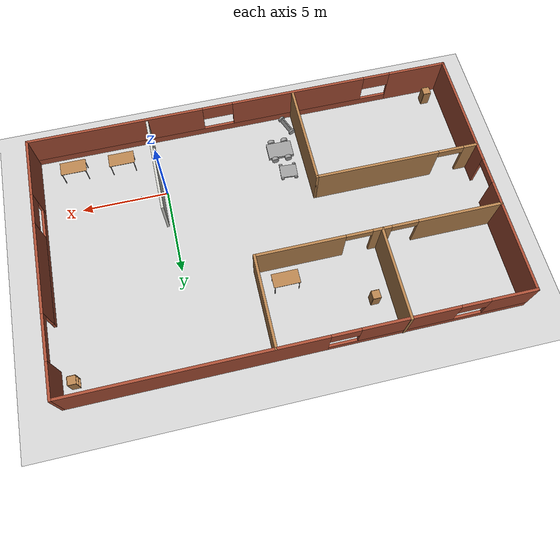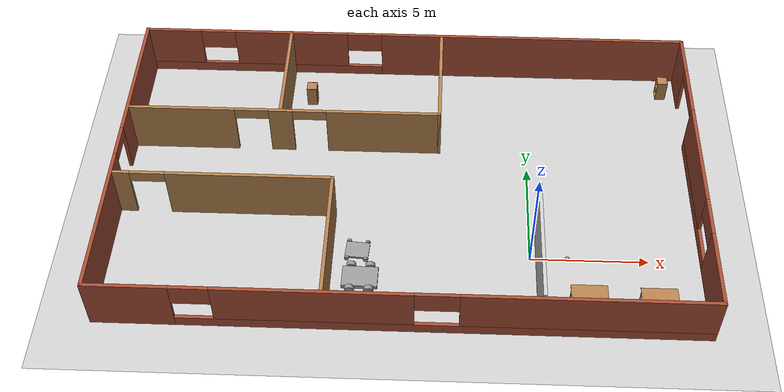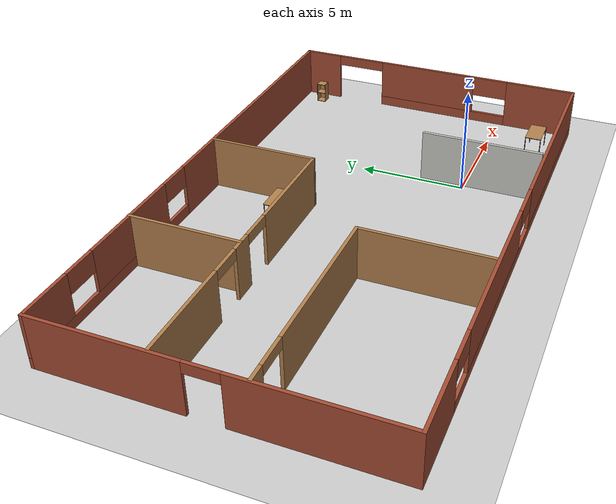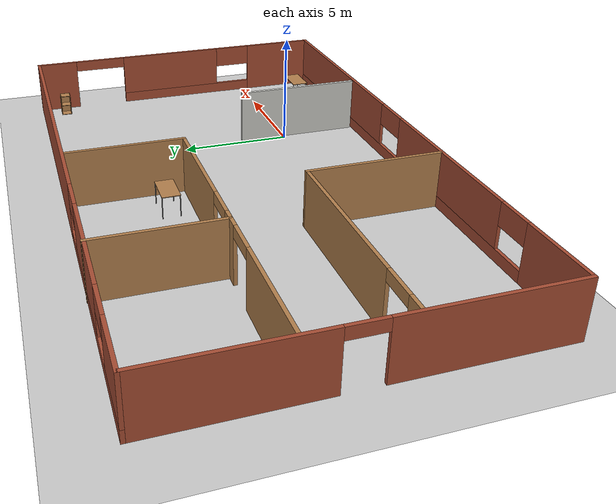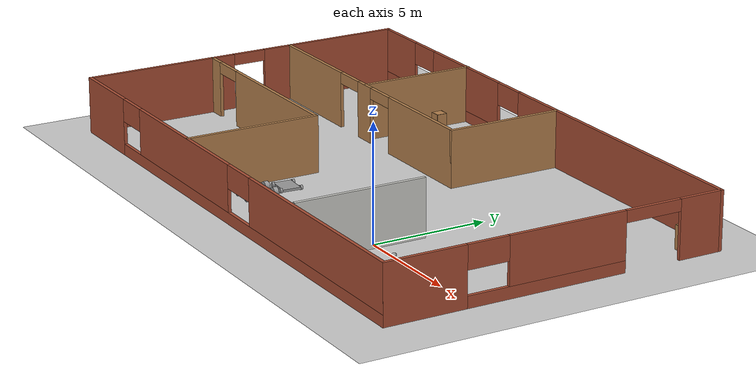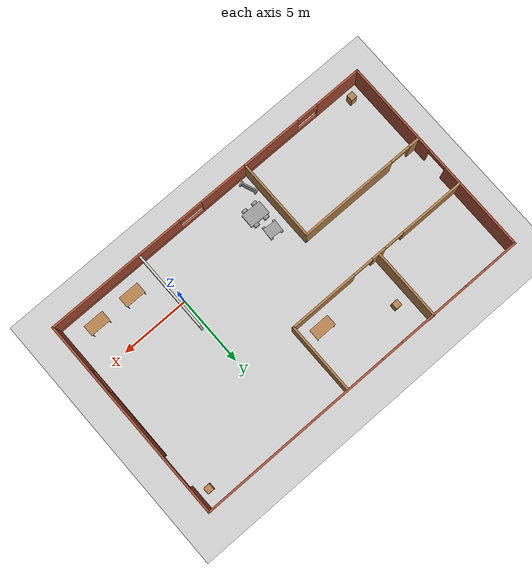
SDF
<sdf version="1.6">
 <world name="default">
  <light name="sun" type="directional">
   <pose>0 0 10 0 -0 0</pose>
   <diffuse>0.8 0.8 0.8 1</diffuse>
   <specular>0.2 0.2 0.2 1</specular>
   <attenuation>
    <range>1000</range>
    <constant>0.9</constant>
    <linear>0.01</linear>
    <quadratic>0.001</quadratic>
   </attenuation>
   <direction>-0.5 0.1 -0.9</direction>
  </light>
  <model name="ground_plane">
   <static>1</static>
   <link name="link">
    <collision name="collision">
     <geometry><plane><normal>0 0 1</normal><size>100 100</size></plane></geometry>
     <surface><friction><ode><mu>100</mu><mu2>50</mu2></ode></friction></surface>
    </collision>
    <visual name="visual">
     <cast_shadows>0</cast_shadows>
     <geometry><plane><normal>0 0 1</normal><size>100 100</size></plane></geometry>
     <material>
      <script><uri>file://media/materials/scripts/gazebo.material</uri><name>Gazebo/Grey</name></script>
     </material>
    </visual>
   </link>
  </model>
  <gravity>0 0 -9.8</gravity>
  <magnetic_field>6e-06 2.3e-05 -4.2e-05</magnetic_field>
  <atmosphere type="adiabatic"/>
  <physics name="default_physics" default="0" type="ode">
   <max_step_size>0.001</max_step_size>
   <real_time_factor>1</real_time_factor>
   <real_time_update_rate>1000</real_time_update_rate>
  </physics>
  <scene><ambient>0.4 0.4 0.4 1</ambient><background>0.7 0.7 0.7 1</background><shadows>1</shadows></scene>
  <spherical_coordinates>
   <surface_model>EARTH_WGS84</surface_model>
   <latitude_deg>0</latitude_deg>
   <longitude_deg>0</longitude_deg>
   <elevation>0</elevation>
   <heading_deg>0</heading_deg>
  </spherical_coordinates>
  <model name="robot">
   <link name="link_0">
    <pose>0 0 -0.000101 0 -0 0</pose>
    <inertial>
     <mass>1</mass>
     <inertia>
      <ixx>0.166667</ixx>
      <ixy>0</ixy>
      <ixz>0</ixz>
      <iyy>0.166667</iyy>
      <iyz>0</iyz>
      <izz>0.166667</izz>
     </inertia>
    </inertial>
    <visual name="visual">
     <geometry><box><size>0.3 1 0.1</size></box></geometry>
     <material>
      <lighting>1</lighting>
      <script><uri>file://media/materials/scripts/gazebo.material</uri><name>Gazebo/Grey</name></script>
      <shader type="pixel"><normal_map>__default__</normal_map></shader>
      <ambient>0.3 0.3 0.3 1</ambient>
      <diffuse>0.7 0.7 0.7 1</diffuse>
      <specular>0.01 0.01 0.01 1</specular>
      <emissive>0 0 0 1</emissive>
     </material>
    </visual>
    <collision name="collision">
     <geometry><box><size>0.3 1 0.1</size></box></geometry>
     <surface>
      <friction>
       <ode><mu>1</mu><mu2>1</mu2><fdir1>0 0 0</fdir1><slip1>0</slip1><slip2>0</slip2></ode>
       <torsional>
        <coefficient>1</coefficient>
        <patch_radius>0</patch_radius>
        <surface_radius>0</surface_radius>
        <use_patch_radius>1</use_patch_radius>
        <ode><slip>0</slip></ode>
       </torsional>
      </friction>
      <bounce><restitution_coefficient>0</restitution_coefficient><threshold>1e+06</threshold></bounce>
      <contact>
       <collide_without_contact>0</collide_without_contact>
       <collide_without_contact_bitmask>1</collide_without_contact_bitmask>
       <collide_bitmask>1</collide_bitmask>
       <ode>
        <soft_cfm>0</soft_cfm>
        <soft_erp>0.2</soft_erp>
        <kp>1e+13</kp>
        <kd>1</kd>
        <max_vel>0.01</max_vel>
        <min_depth>0</min_depth>
       </ode>
       <bullet>
        <split_impulse>1</split_impulse>
        <split_impulse_penetration_threshold>-0.01</split_impulse_penetration_threshold>
        <soft_cfm>0</soft_cfm>
        <soft_erp>0.2</soft_erp>
        <kp>1e+13</kp>
        <kd>1</kd>
       </bullet>
      </contact>
     </surface>
    </collision>
   </link>
   <link name="link_1">
    <pose>0 -0.550019 -0.000101 1.5707 -0 0</pose>
    <inertial>
     <mass>1</mass>
     <inertia><ixx>0.145833</ixx><ixy>0</ixy><ixz>0</ixz><iyy>0.145833</iyy><iyz>0</iyz><izz>0.125</izz></inertia>
    </inertial>
    <visual name="visual">
     <geometry><cylinder><radius>0.2</radius><length>0.1</length></cylinder></geometry>
     <material>
      <lighting>1</lighting>
      <script><uri>file://media/materials/scripts/gazebo.material</uri><name>Gazebo/Grey</name></script>
      <shader type="pixel"><normal_map>__default__</normal_map></shader>
      <ambient>0.3 0.3 0.3 1</ambient>
      <diffuse>0.7 0.7 0.7 1</diffuse>
      <specular>0.01 0.01 0.01 1</specular>
      <emissive>0 0 0 1</emissive>
     </material>
    </visual>
    <collision name="collision">
     <geometry><cylinder><radius>0.2</radius><length>0.1</length></cylinder></geometry>
     <surface>
      <friction>
       <ode><mu>1</mu><mu2>1</mu2><fdir1>0 0 0</fdir1><slip1>0</slip1><slip2>0</slip2></ode>
       <torsional>
        <coefficient>1</coefficient>
        <patch_radius>0</patch_radius>
        <surface_radius>0</surface_radius>
        <use_patch_radius>1</use_patch_radius>
        <ode><slip>0</slip></ode>
       </torsional>
      </friction>
      <bounce><restitution_coefficient>0</restitution_coefficient><threshold>1e+06</threshold></bounce>
      <contact>
       <collide_without_contact>0</collide_without_contact>
       <collide_without_contact_bitmask>1</collide_without_contact_bitmask>
       <collide_bitmask>1</collide_bitmask>
       <ode>
        <soft_cfm>0</soft_cfm>
        <soft_erp>0.2</soft_erp>
        <kp>1e+13</kp>
        <kd>1</kd>
        <max_vel>0.01</max_vel>
        <min_depth>0</min_depth>
       </ode>
       <bullet>
        <split_impulse>1</split_impulse>
        <split_impulse_penetration_threshold>-0.01</split_impulse_penetration_threshold>
        <soft_cfm>0</soft_cfm>
        <soft_erp>0.2</soft_erp>
        <kp>1e+13</kp>
        <kd>1</kd>
       </bullet>
      </contact>
     </surface>
    </collision>
   </link>
   <link name="link_1_clone">
    <pose>0 0.550019 0.000202 1.5707 -0 0</pose>
    <inertial>
     <mass>1</mass>
     <inertia><ixx>0.145833</ixx><ixy>0</ixy><ixz>0</ixz><iyy>0.145833</iyy><iyz>0</iyz><izz>0.125</izz></inertia>
    </inertial>
    <visual name="visual">
     <geometry><cylinder><radius>0.2</radius><length>0.1</length></cylinder></geometry>
     <material>
      <lighting>1</lighting>
      <script><uri>file://media/materials/scripts/gazebo.material</uri><name>Gazebo/Grey</name></script>
      <shader type="pixel"><normal_map>__default__</normal_map></shader>
      <ambient>0.3 0.3 0.3 1</ambient>
      <diffuse>0.7 0.7 0.7 1</diffuse>
      <specular>0.01 0.01 0.01 1</specular>
      <emissive>0 0 0 1</emissive>
     </material>
    </visual>
    <collision name="collision">
     <geometry><cylinder><radius>0.2</radius><length>0.1</length></cylinder></geometry>
     <surface>
      <friction>
       <ode><mu>1</mu><mu2>1</mu2><fdir1>0 0 0</fdir1><slip1>0</slip1><slip2>0</slip2></ode>
       <torsional>
        <coefficient>1</coefficient>
        <patch_radius>0</patch_radius>
        <surface_radius>0</surface_radius>
        <use_patch_radius>1</use_patch_radius>
        <ode><slip>0</slip></ode>
       </torsional>
      </friction>
      <bounce><restitution_coefficient>0</restitution_coefficient><threshold>1e+06</threshold></bounce>
      <contact>
       <collide_without_contact>0</collide_without_contact>
       <collide_without_contact_bitmask>1</collide_without_contact_bitmask>
       <collide_bitmask>1</collide_bitmask>
       <ode>
        <soft_cfm>0</soft_cfm>
        <soft_erp>0.2</soft_erp>
        <kp>1e+13</kp>
        <kd>1</kd>
        <max_vel>0.01</max_vel>
        <min_depth>0</min_depth>
       </ode>
       <bullet>
        <split_impulse>1</split_impulse>
        <split_impulse_penetration_threshold>-0.01</split_impulse_penetration_threshold>
        <soft_cfm>0</soft_cfm>
        <soft_erp>0.2</soft_erp>
        <kp>1e+13</kp>
        <kd>1</kd>
       </bullet>
      </contact>
     </surface>
    </collision>
   </link>
   <joint name="link_0_JOINT_1" type="revolute">
    <parent>link_0</parent>
    <child>link_1</child>
    <axis>
     <xyz>0 0 1</xyz>
     <use_parent_model_frame>0</use_parent_model_frame>
     <limit>
      <lower>-1.79769e+308</lower>
      <upper>1.79769e+308</upper>
      <effort>-1</effort>
      <velocity>-1</velocity>
     </limit>
     <dynamics>
      <spring_reference>0</spring_reference>
      <spring_stiffness>0</spring_stiffness>
      <damping>0</damping>
     </dynamics>
    </axis>
    <physics>
     <ode><limit><cfm>0</cfm><erp>0.2</erp></limit><suspension><cfm>0</cfm><erp>0.2</erp></suspension></ode>
    </physics>
   </joint>
   <joint name="link_0_JOINT_3" type="revolute">
    <parent>link_0</parent>
    <child>link_1_clone</child>
    <axis>
     <xyz>1 0 0</xyz>
     <use_parent_model_frame>0</use_parent_model_frame>
     <limit>
      <lower>-1.79769e+308</lower>
      <upper>1.79769e+308</upper>
      <effort>-1</effort>
      <velocity>-1</velocity>
     </limit>
     <dynamics>
      <spring_reference>0</spring_reference>
      <spring_stiffness>0</spring_stiffness>
      <damping>0</damping>
     </dynamics>
    </axis>
    <physics>
     <ode><limit><cfm>0</cfm><erp>0.2</erp></limit><suspension><cfm>0</cfm><erp>0.2</erp></suspension></ode>
    </physics>
   </joint>
   <static>0</static>
   <pose>-7.95995 -2.96753 0.200034 3.14128 -1.17564 -2.76196</pose>
  </model>
  <model name="robot4wheels">
   <link name="link_0">
    <pose>0 0 -0.016 0 -0 0</pose>
    <inertial>
     <mass>1</mass>
     <inertia>
      <ixx>0.166667</ixx>
      <ixy>0</ixy>
      <ixz>0</ixz>
      <iyy>0.166667</iyy>
      <iyz>0</iyz>
      <izz>0.166667</izz>
     </inertia>
    </inertial>
    <visual name="visual">
     <geometry><box><size>1.5 1 0.2</size></box></geometry>
     <material>
      <lighting>1</lighting>
      <script><uri>file://media/materials/scripts/gazebo.material</uri><name>Gazebo/Grey</name></script>
      <shader type="pixel"><normal_map>__default__</normal_map></shader>
      <ambient>0.3 0.3 0.3 1</ambient>
      <diffuse>0.7 0.7 0.7 1</diffuse>
      <specular>0.01 0.01 0.01 1</specular>
      <emissive>0 0 0 1</emissive>
     </material>
    </visual>
    <collision name="collision">
     <geometry><box><size>1.5 1 0.2</size></box></geometry>
     <surface>
      <friction>
       <ode><mu>1</mu><mu2>1</mu2><fdir1>0 0 0</fdir1><slip1>0</slip1><slip2>0</slip2></ode>
       <torsional>
        <coefficient>1</coefficient>
        <patch_radius>0</patch_radius>
        <surface_radius>0</surface_radius>
        <use_patch_radius>1</use_patch_radius>
        <ode><slip>0</slip></ode>
       </torsional>
      </friction>
      <bounce><restitution_coefficient>0</restitution_coefficient><threshold>1e+06</threshold></bounce>
      <contact>
       <collide_without_contact>0</collide_without_contact>
       <collide_without_contact_bitmask>1</collide_without_contact_bitmask>
       <collide_bitmask>1</collide_bitmask>
       <ode>
        <soft_cfm>0</soft_cfm>
        <soft_erp>0.2</soft_erp>
        <kp>1e+13</kp>
        <kd>1</kd>
        <max_vel>0.01</max_vel>
        <min_depth>0</min_depth>
       </ode>
       <bullet>
        <split_impulse>1</split_impulse>
        <split_impulse_penetration_threshold>-0.01</split_impulse_penetration_threshold>
        <soft_cfm>0</soft_cfm>
        <soft_erp>0.2</soft_erp>
        <kp>1e+13</kp>
        <kd>1</kd>
       </bullet>
      </contact>
     </surface>
    </collision>
   </link>
   <link name="link_1">
    <pose>-0.4 -0.600001 0.004 1.5708 -0 0</pose>
    <inertial>
     <mass>1</mass>
     <inertia><ixx>0.145833</ixx><ixy>0</ixy><ixz>0</ixz><iyy>0.145833</iyy><iyz>0</iyz><izz>0.125</izz></inertia>
    </inertial>
    <visual name="visual">
     <geometry><cylinder><radius>0.2</radius><length>0.2</length></cylinder></geometry>
     <material>
      <lighting>1</lighting>
      <script><uri>file://media/materials/scripts/gazebo.material</uri><name>Gazebo/Grey</name></script>
      <shader type="pixel"><normal_map>__default__</normal_map></shader>
      <ambient>0.3 0.3 0.3 1</ambient>
      <diffuse>0.7 0.7 0.7 1</diffuse>
      <specular>0.01 0.01 0.01 1</specular>
      <emissive>0 0 0 1</emissive>
     </material>
    </visual>
    <collision name="collision">
     <geometry><cylinder><radius>0.2</radius><length>0.2</length></cylinder></geometry>
     <surface>
      <friction>
       <ode><mu>1</mu><mu2>1</mu2><fdir1>0 0 0</fdir1><slip1>0</slip1><slip2>0</slip2></ode>
       <torsional>
        <coefficient>1</coefficient>
        <patch_radius>0</patch_radius>
        <surface_radius>0</surface_radius>
        <use_patch_radius>1</use_patch_radius>
        <ode><slip>0</slip></ode>
       </torsional>
      </friction>
      <bounce><restitution_coefficient>0</restitution_coefficient><threshold>1e+06</threshold></bounce>
      <contact>
       <collide_without_contact>0</collide_without_contact>
       <collide_without_contact_bitmask>1</collide_without_contact_bitmask>
       <collide_bitmask>1</collide_bitmask>
       <ode>
        <soft_cfm>0</soft_cfm>
        <soft_erp>0.2</soft_erp>
        <kp>1e+13</kp>
        <kd>1</kd>
        <max_vel>0.01</max_vel>
        <min_depth>0</min_depth>
       </ode>
       <bullet>
        <split_impulse>1</split_impulse>
        <split_impulse_penetration_threshold>-0.01</split_impulse_penetration_threshold>
        <soft_cfm>0</soft_cfm>
        <soft_erp>0.2</soft_erp>
        <kp>1e+13</kp>
        <kd>1</kd>
       </bullet>
      </contact>
     </surface>
    </collision>
   </link>
   <link name="link_1_clone">
    <pose>-0.4 0.600001 0.004 1.5708 -0 0</pose>
    <inertial>
     <mass>1</mass>
     <inertia><ixx>0.145833</ixx><ixy>0</ixy><ixz>0</ixz><iyy>0.145833</iyy><iyz>0</iyz><izz>0.125</izz></inertia>
    </inertial>
    <visual name="visual">
     <geometry><cylinder><radius>0.2</radius><length>0.2</length></cylinder></geometry>
     <material>
      <lighting>1</lighting>
      <script><uri>file://media/materials/scripts/gazebo.material</uri><name>Gazebo/Grey</name></script>
      <shader type="pixel"><normal_map>__default__</normal_map></shader>
      <ambient>0.3 0.3 0.3 1</ambient>
      <diffuse>0.7 0.7 0.7 1</diffuse>
      <specular>0.01 0.01 0.01 1</specular>
      <emissive>0 0 0 1</emissive>
     </material>
    </visual>
    <collision name="collision">
     <geometry><cylinder><radius>0.2</radius><length>0.2</length></cylinder></geometry>
     <surface>
      <friction>
       <ode><mu>1</mu><mu2>1</mu2><fdir1>0 0 0</fdir1><slip1>0</slip1><slip2>0</slip2></ode>
       <torsional>
        <coefficient>1</coefficient>
        <patch_radius>0</patch_radius>
        <surface_radius>0</surface_radius>
        <use_patch_radius>1</use_patch_radius>
        <ode><slip>0</slip></ode>
       </torsional>
      </friction>
      <bounce><restitution_coefficient>0</restitution_coefficient><threshold>1e+06</threshold></bounce>
      <contact>
       <collide_without_contact>0</collide_without_contact>
       <collide_without_contact_bitmask>1</collide_without_contact_bitmask>
       <collide_bitmask>1</collide_bitmask>
       <ode>
        <soft_cfm>0</soft_cfm>
        <soft_erp>0.2</soft_erp>
        <kp>1e+13</kp>
        <kd>1</kd>
        <max_vel>0.01</max_vel>
        <min_depth>0</min_depth>
       </ode>
       <bullet>
        <split_impulse>1</split_impulse>
        <split_impulse_penetration_threshold>-0.01</split_impulse_penetration_threshold>
        <soft_cfm>0</soft_cfm>
        <soft_erp>0.2</soft_erp>
        <kp>1e+13</kp>
        <kd>1</kd>
       </bullet>
      </contact>
     </surface>
    </collision>
   </link>
   <link name="link_1_clone_0">
    <pose>0.4 -0.600001 0.004 1.5708 -0 0</pose>
    <inertial>
     <mass>1</mass>
     <inertia><ixx>0.145833</ixx><ixy>0</ixy><ixz>0</ixz><iyy>0.145833</iyy><iyz>0</iyz><izz>0.125</izz></inertia>
    </inertial>
    <visual name="visual">
     <geometry><cylinder><radius>0.2</radius><length>0.2</length></cylinder></geometry>
     <material>
      <lighting>1</lighting>
      <script><uri>file://media/materials/scripts/gazebo.material</uri><name>Gazebo/Grey</name></script>
      <shader type="pixel"><normal_map>__default__</normal_map></shader>
      <ambient>0.3 0.3 0.3 1</ambient>
      <diffuse>0.7 0.7 0.7 1</diffuse>
      <specular>0.01 0.01 0.01 1</specular>
      <emissive>0 0 0 1</emissive>
     </material>
    </visual>
    <collision name="collision">
     <geometry><cylinder><radius>0.2</radius><length>0.2</length></cylinder></geometry>
     <surface>
      <friction>
       <ode><mu>1</mu><mu2>1</mu2><fdir1>0 0 0</fdir1><slip1>0</slip1><slip2>0</slip2></ode>
       <torsional>
        <coefficient>1</coefficient>
        <patch_radius>0</patch_radius>
        <surface_radius>0</surface_radius>
        <use_patch_radius>1</use_patch_radius>
        <ode><slip>0</slip></ode>
       </torsional>
      </friction>
      <bounce><restitution_coefficient>0</restitution_coefficient><threshold>1e+06</threshold></bounce>
      <contact>
       <collide_without_contact>0</collide_without_contact>
       <collide_without_contact_bitmask>1</collide_without_contact_bitmask>
       <collide_bitmask>1</collide_bitmask>
       <ode>
        <soft_cfm>0</soft_cfm>
        <soft_erp>0.2</soft_erp>
        <kp>1e+13</kp>
        <kd>1</kd>
        <max_vel>0.01</max_vel>
        <min_depth>0</min_depth>
       </ode>
       <bullet>
        <split_impulse>1</split_impulse>
        <split_impulse_penetration_threshold>-0.01</split_impulse_penetration_threshold>
        <soft_cfm>0</soft_cfm>
        <soft_erp>0.2</soft_erp>
        <kp>1e+13</kp>
        <kd>1</kd>
       </bullet>
      </contact>
     </surface>
    </collision>
   </link>
   <link name="link_1_clone_1">
    <pose>0.4 0.600001 0.004 1.5708 -0 0</pose>
    <inertial>
     <mass>1</mass>
     <inertia><ixx>0.145833</ixx><ixy>0</ixy><ixz>0</ixz><iyy>0.145833</iyy><iyz>0</iyz><izz>0.125</izz></inertia>
    </inertial>
    <visual name="visual">
     <geometry><cylinder><radius>0.2</radius><length>0.2</length></cylinder></geometry>
     <material>
      <lighting>1</lighting>
      <script><uri>file://media/materials/scripts/gazebo.material</uri><name>Gazebo/Grey</name></script>
      <shader type="pixel"><normal_map>__default__</normal_map></shader>
      <ambient>0.3 0.3 0.3 1</ambient>
      <diffuse>0.7 0.7 0.7 1</diffuse>
      <specular>0.01 0.01 0.01 1</specular>
      <emissive>0 0 0 1</emissive>
     </material>
    </visual>
    <collision name="collision">
     <geometry><cylinder><radius>0.2</radius><length>0.2</length></cylinder></geometry>
     <surface>
      <friction>
       <ode><mu>1</mu><mu2>1</mu2><fdir1>0 0 0</fdir1><slip1>0</slip1><slip2>0</slip2></ode>
       <torsional>
        <coefficient>1</coefficient>
        <patch_radius>0</patch_radius>
        <surface_radius>0</surface_radius>
        <use_patch_radius>1</use_patch_radius>
        <ode><slip>0</slip></ode>
       </torsional>
      </friction>
      <bounce><restitution_coefficient>0</restitution_coefficient><threshold>1e+06</threshold></bounce>
      <contact>
       <collide_without_contact>0</collide_without_contact>
       <collide_without_contact_bitmask>1</collide_without_contact_bitmask>
       <collide_bitmask>1</collide_bitmask>
       <ode>
        <soft_cfm>0</soft_cfm>
        <soft_erp>0.2</soft_erp>
        <kp>1e+13</kp>
        <kd>1</kd>
        <max_vel>0.01</max_vel>
        <min_depth>0</min_depth>
       </ode>
       <bullet>
        <split_impulse>1</split_impulse>
        <split_impulse_penetration_threshold>-0.01</split_impulse_penetration_threshold>
        <soft_cfm>0</soft_cfm>
        <soft_erp>0.2</soft_erp>
        <kp>1e+13</kp>
        <kd>1</kd>
       </bullet>
      </contact>
     </surface>
    </collision>
   </link>
   <joint name="link_0_JOINT_0" type="revolute">
    <parent>link_0</parent>
    <child>link_1</child>
    <axis>
     <xyz>0 0 1</xyz>
     <use_parent_model_frame>0</use_parent_model_frame>
     <limit>
      <lower>-1.79769e+308</lower>
      <upper>1.79769e+308</upper>
      <effort>-1</effort>
      <velocity>-1</velocity>
     </limit>
     <dynamics>
      <spring_reference>0</spring_reference>
      <spring_stiffness>0</spring_stiffness>
      <damping>0</damping>
     </dynamics>
    </axis>
    <physics>
     <ode><limit><cfm>0</cfm><erp>0.2</erp></limit><suspension><cfm>0</cfm><erp>0.2</erp></suspension></ode>
    </physics>
   </joint>
   <joint name="link_0_JOINT_1" type="revolute">
    <parent>link_0</parent>
    <child>link_1_clone_0</child>
    <axis>
     <xyz>0 0 1</xyz>
     <use_parent_model_frame>0</use_parent_model_frame>
     <limit>
      <lower>-1.79769e+308</lower>
      <upper>1.79769e+308</upper>
      <effort>-1</effort>
      <velocity>-1</velocity>
     </limit>
     <dynamics>
      <spring_reference>0</spring_reference>
      <spring_stiffness>0</spring_stiffness>
      <damping>0</damping>
      <friction>0</friction>
     </dynamics>
    </axis>
    <physics>
     <ode><limit><cfm>0</cfm><erp>0.2</erp></limit><suspension><cfm>0</cfm><erp>0.2</erp></suspension></ode>
    </physics>
   </joint>
   <joint name="link_0_JOINT_3" type="revolute">
    <parent>link_0</parent>
    <child>link_1_clone_1</child>
    <axis>
     <xyz>0 0 1</xyz>
     <use_parent_model_frame>0</use_parent_model_frame>
     <limit>
      <lower>-1.79769e+308</lower>
      <upper>1.79769e+308</upper>
      <effort>-1</effort>
      <velocity>-1</velocity>
     </limit>
     <dynamics>
      <spring_reference>0</spring_reference>
      <spring_stiffness>0</spring_stiffness>
      <damping>0</damping>
     </dynamics>
    </axis>
    <physics>
     <ode><limit><cfm>0</cfm><erp>0.2</erp></limit><suspension><cfm>0</cfm><erp>0.2</erp></suspension></ode>
    </physics>
   </joint>
   <joint name="link_0_JOINT_4" type="revolute">
    <parent>link_0</parent>
    <child>link_1_clone</child>
    <axis>
     <xyz>0 0 1</xyz>
     <use_parent_model_frame>0</use_parent_model_frame>
     <limit>
      <lower>-1.79769e+308</lower>
      <upper>1.79769e+308</upper>
      <effort>-1</effort>
      <velocity>-1</velocity>
     </limit>
     <dynamics>
      <spring_reference>0</spring_reference>
      <spring_stiffness>0</spring_stiffness>
      <damping>0</damping>
     </dynamics>
    </axis>
    <physics>
     <ode><limit><cfm>0</cfm><erp>0.2</erp></limit><suspension><cfm>0</cfm><erp>0.2</erp></suspension></ode>
    </physics>
   </joint>
   <static>0</static>
   <pose>-7.13642 -1.33279 0.196001 1e-06 0 -0.014132</pose>
  </model>
  <model name="robotsmall4wheels">
   <link name="link_0">
    <pose>0.008 0 0 0 -0 0</pose>
    <inertial>
     <mass>1</mass>
     <inertia>
      <ixx>0.166667</ixx>
      <ixy>0</ixy>
      <ixz>0</ixz>
      <iyy>0.166667</iyy>
      <iyz>0</iyz>
      <izz>0.166667</izz>
     </inertia>
    </inertial>
    <visual name="visual">
     <geometry><box><size>1 0.8 0.1</size></box></geometry>
     <material>
      <lighting>1</lighting>
      <script><uri>file://media/materials/scripts/gazebo.material</uri><name>Gazebo/Grey</name></script>
      <shader type="pixel"><normal_map>__default__</normal_map></shader>
      <ambient>0.3 0.3 0.3 1</ambient>
      <diffuse>0.7 0.7 0.7 1</diffuse>
      <specular>0.01 0.01 0.01 1</specular>
      <emissive>0 0 0 1</emissive>
     </material>
    </visual>
    <collision name="collision">
     <geometry><box><size>1 0.8 0.1</size></box></geometry>
     <surface>
      <friction>
       <ode><mu>1</mu><mu2>1</mu2><fdir1>0 0 0</fdir1><slip1>0</slip1><slip2>0</slip2></ode>
       <torsional>
        <coefficient>1</coefficient>
        <patch_radius>0</patch_radius>
        <surface_radius>0</surface_radius>
        <use_patch_radius>1</use_patch_radius>
        <ode><slip>0</slip></ode>
       </torsional>
      </friction>
      <bounce><restitution_coefficient>0</restitution_coefficient><threshold>1e+06</threshold></bounce>
      <contact>
       <collide_without_contact>0</collide_without_contact>
       <collide_without_contact_bitmask>1</collide_without_contact_bitmask>
       <collide_bitmask>1</collide_bitmask>
       <ode>
        <soft_cfm>0</soft_cfm>
        <soft_erp>0.2</soft_erp>
        <kp>1e+13</kp>
        <kd>1</kd>
        <max_vel>0.01</max_vel>
        <min_depth>0</min_depth>
       </ode>
       <bullet>
        <split_impulse>1</split_impulse>
        <split_impulse_penetration_threshold>-0.01</split_impulse_penetration_threshold>
        <soft_cfm>0</soft_cfm>
        <soft_erp>0.2</soft_erp>
        <kp>1e+13</kp>
        <kd>1</kd>
       </bullet>
      </contact>
     </surface>
    </collision>
   </link>
   <link name="link_1">
    <pose>0.418031 -0.452375 0 1.5708 -0 0</pose>
    <inertial>
     <mass>1</mass>
     <inertia><ixx>0.145833</ixx><ixy>0</ixy><ixz>0</ixz><iyy>0.145833</iyy><iyz>0</iyz><izz>0.125</izz></inertia>
    </inertial>
    <visual name="visual">
     <geometry><cylinder><radius>0.1</radius><length>0.1</length></cylinder></geometry>
     <material>
      <lighting>1</lighting>
      <script><uri>file://media/materials/scripts/gazebo.material</uri><name>Gazebo/Grey</name></script>
      <shader type="pixel"><normal_map>__default__</normal_map></shader>
      <ambient>0.3 0.3 0.3 1</ambient>
      <diffuse>0.7 0.7 0.7 1</diffuse>
      <specular>0.01 0.01 0.01 1</specular>
      <emissive>0 0 0 1</emissive>
     </material>
    </visual>
    <collision name="collision">
     <geometry><cylinder><radius>0.1</radius><length>0.1</length></cylinder></geometry>
     <surface>
      <friction>
       <ode><mu>1</mu><mu2>1</mu2><fdir1>0 0 0</fdir1><slip1>0</slip1><slip2>0</slip2></ode>
       <torsional>
        <coefficient>1</coefficient>
        <patch_radius>0</patch_radius>
        <surface_radius>0</surface_radius>
        <use_patch_radius>1</use_patch_radius>
        <ode><slip>0</slip></ode>
       </torsional>
      </friction>
      <bounce><restitution_coefficient>0</restitution_coefficient><threshold>1e+06</threshold></bounce>
      <contact>
       <collide_without_contact>0</collide_without_contact>
       <collide_without_contact_bitmask>1</collide_without_contact_bitmask>
       <collide_bitmask>1</collide_bitmask>
       <ode>
        <soft_cfm>0</soft_cfm>
        <soft_erp>0.2</soft_erp>
        <kp>1e+13</kp>
        <kd>1</kd>
        <max_vel>0.01</max_vel>
        <min_depth>0</min_depth>
       </ode>
       <bullet>
        <split_impulse>1</split_impulse>
        <split_impulse_penetration_threshold>-0.01</split_impulse_penetration_threshold>
        <soft_cfm>0</soft_cfm>
        <soft_erp>0.2</soft_erp>
        <kp>1e+13</kp>
        <kd>1</kd>
       </bullet>
      </contact>
     </surface>
    </collision>
   </link>
   <link name="link_1_clone">
    <pose>-0.392 -0.45 -0 1.5708 -0 0</pose>
    <inertial>
     <mass>1</mass>
     <inertia><ixx>0.145833</ixx><ixy>0</ixy><ixz>0</ixz><iyy>0.145833</iyy><iyz>0</iyz><izz>0.125</izz></inertia>
    </inertial>
    <visual name="visual">
     <geometry><cylinder><radius>0.1</radius><length>0.1</length></cylinder></geometry>
     <material>
      <lighting>1</lighting>
      <script><uri>file://media/materials/scripts/gazebo.material</uri><name>Gazebo/Grey</name></script>
      <shader type="pixel"><normal_map>__default__</normal_map></shader>
      <ambient>0.3 0.3 0.3 1</ambient>
      <diffuse>0.7 0.7 0.7 1</diffuse>
      <specular>0.01 0.01 0.01 1</specular>
      <emissive>0 0 0 1</emissive>
     </material>
    </visual>
    <collision name="collision">
     <geometry><cylinder><radius>0.1</radius><length>0.1</length></cylinder></geometry>
     <surface>
      <friction>
       <ode><mu>1</mu><mu2>1</mu2><fdir1>0 0 0</fdir1><slip1>0</slip1><slip2>0</slip2></ode>
       <torsional>
        <coefficient>1</coefficient>
        <patch_radius>0</patch_radius>
        <surface_radius>0</surface_radius>
        <use_patch_radius>1</use_patch_radius>
        <ode><slip>0</slip></ode>
       </torsional>
      </friction>
      <bounce><restitution_coefficient>0</restitution_coefficient><threshold>1e+06</threshold></bounce>
      <contact>
       <collide_without_contact>0</collide_without_contact>
       <collide_without_contact_bitmask>1</collide_without_contact_bitmask>
       <collide_bitmask>1</collide_bitmask>
       <ode>
        <soft_cfm>0</soft_cfm>
        <soft_erp>0.2</soft_erp>
        <kp>1e+13</kp>
        <kd>1</kd>
        <max_vel>0.01</max_vel>
        <min_depth>0</min_depth>
       </ode>
       <bullet>
        <split_impulse>1</split_impulse>
        <split_impulse_penetration_threshold>-0.01</split_impulse_penetration_threshold>
        <soft_cfm>0</soft_cfm>
        <soft_erp>0.2</soft_erp>
        <kp>1e+13</kp>
        <kd>1</kd>
       </bullet>
      </contact>
     </surface>
    </collision>
   </link>
   <link name="link_1_clone_0">
    <pose>-0.392 0.45 -0 1.5708 -0 0</pose>
    <inertial>
     <mass>1</mass>
     <inertia><ixx>0.145833</ixx><ixy>0</ixy><ixz>0</ixz><iyy>0.145833</iyy><iyz>0</iyz><izz>0.125</izz></inertia>
    </inertial>
    <visual name="visual">
     <geometry><cylinder><radius>0.1</radius><length>0.1</length></cylinder></geometry>
     <material>
      <lighting>1</lighting>
      <script><uri>file://media/materials/scripts/gazebo.material</uri><name>Gazebo/Grey</name></script>
      <shader type="pixel"><normal_map>__default__</normal_map></shader>
      <ambient>0.3 0.3 0.3 1</ambient>
      <diffuse>0.7 0.7 0.7 1</diffuse>
      <specular>0.01 0.01 0.01 1</specular>
      <emissive>0 0 0 1</emissive>
     </material>
    </visual>
    <collision name="collision">
     <geometry><cylinder><radius>0.1</radius><length>0.1</length></cylinder></geometry>
     <surface>
      <friction>
       <ode><mu>1</mu><mu2>1</mu2><fdir1>0 0 0</fdir1><slip1>0</slip1><slip2>0</slip2></ode>
       <torsional>
        <coefficient>1</coefficient>
        <patch_radius>0</patch_radius>
        <surface_radius>0</surface_radius>
        <use_patch_radius>1</use_patch_radius>
        <ode><slip>0</slip></ode>
       </torsional>
      </friction>
      <bounce><restitution_coefficient>0</restitution_coefficient><threshold>1e+06</threshold></bounce>
      <contact>
       <collide_without_contact>0</collide_without_contact>
       <collide_without_contact_bitmask>1</collide_without_contact_bitmask>
       <collide_bitmask>1</collide_bitmask>
       <ode>
        <soft_cfm>0</soft_cfm>
        <soft_erp>0.2</soft_erp>
        <kp>1e+13</kp>
        <kd>1</kd>
        <max_vel>0.01</max_vel>
        <min_depth>0</min_depth>
       </ode>
       <bullet>
        <split_impulse>1</split_impulse>
        <split_impulse_penetration_threshold>-0.01</split_impulse_penetration_threshold>
        <soft_cfm>0</soft_cfm>
        <soft_erp>0.2</soft_erp>
        <kp>1e+13</kp>
        <kd>1</kd>
       </bullet>
      </contact>
     </surface>
    </collision>
   </link>
   <link name="link_1_clone_1">
    <pose>0.408 0.45 -0 1.5708 -0 0</pose>
    <inertial>
     <mass>1</mass>
     <inertia><ixx>0.145833</ixx><ixy>0</ixy><ixz>0</ixz><iyy>0.145833</iyy><iyz>0</iyz><izz>0.125</izz></inertia>
    </inertial>
    <visual name="visual">
     <geometry><cylinder><radius>0.1</radius><length>0.1</length></cylinder></geometry>
     <material>
      <lighting>1</lighting>
      <script><uri>file://media/materials/scripts/gazebo.material</uri><name>Gazebo/Grey</name></script>
      <shader type="pixel"><normal_map>__default__</normal_map></shader>
      <ambient>0.3 0.3 0.3 1</ambient>
      <diffuse>0.7 0.7 0.7 1</diffuse>
      <specular>0.01 0.01 0.01 1</specular>
      <emissive>0 0 0 1</emissive>
     </material>
    </visual>
    <collision name="collision">
     <geometry><cylinder><radius>0.1</radius><length>0.1</length></cylinder></geometry>
     <surface>
      <friction>
       <ode><mu>1</mu><mu2>1</mu2><fdir1>0 0 0</fdir1><slip1>0</slip1><slip2>0</slip2></ode>
       <torsional>
        <coefficient>1</coefficient>
        <patch_radius>0</patch_radius>
        <surface_radius>0</surface_radius>
        <use_patch_radius>1</use_patch_radius>
        <ode><slip>0</slip></ode>
       </torsional>
      </friction>
      <bounce><restitution_coefficient>0</restitution_coefficient><threshold>1e+06</threshold></bounce>
      <contact>
       <collide_without_contact>0</collide_without_contact>
       <collide_without_contact_bitmask>1</collide_without_contact_bitmask>
       <collide_bitmask>1</collide_bitmask>
       <ode>
        <soft_cfm>0</soft_cfm>
        <soft_erp>0.2</soft_erp>
        <kp>1e+13</kp>
        <kd>1</kd>
        <max_vel>0.01</max_vel>
        <min_depth>0</min_depth>
       </ode>
       <bullet>
        <split_impulse>1</split_impulse>
        <split_impulse_penetration_threshold>-0.01</split_impulse_penetration_threshold>
        <soft_cfm>0</soft_cfm>
        <soft_erp>0.2</soft_erp>
        <kp>1e+13</kp>
        <kd>1</kd>
       </bullet>
      </contact>
     </surface>
    </collision>
   </link>
   <joint name="link_0_JOINT_0" type="revolute">
    <parent>link_0</parent>
    <child>link_1</child>
    <axis>
     <xyz>0 0 1</xyz>
     <use_parent_model_frame>0</use_parent_model_frame>
     <limit>
      <lower>-1.79769e+308</lower>
      <upper>1.79769e+308</upper>
      <effort>-1</effort>
      <velocity>-1</velocity>
     </limit>
     <dynamics>
      <spring_reference>0</spring_reference>
      <spring_stiffness>0</spring_stiffness>
      <damping>0</damping>
     </dynamics>
    </axis>
    <physics>
     <ode><limit><cfm>0</cfm><erp>0.2</erp></limit><suspension><cfm>0</cfm><erp>0.2</erp></suspension></ode>
    </physics>
   </joint>
   <joint name="link_0_JOINT_3" type="revolute">
    <parent>link_0</parent>
    <child>link_1_clone</child>
    <axis>
     <xyz>0 0 1</xyz>
     <use_parent_model_frame>0</use_parent_model_frame>
     <limit>
      <lower>-1.79769e+308</lower>
      <upper>1.79769e+308</upper>
      <effort>-1</effort>
      <velocity>-1</velocity>
     </limit>
     <dynamics>
      <spring_reference>0</spring_reference>
      <spring_stiffness>0</spring_stiffness>
      <damping>0</damping>
      <friction>0</friction>
     </dynamics>
    </axis>
    <physics>
     <ode><limit><cfm>0</cfm><erp>0.2</erp></limit><suspension><cfm>0</cfm><erp>0.2</erp></suspension></ode>
    </physics>
   </joint>
   <joint name="link_0_JOINT_5" type="revolute">
    <parent>link_0</parent>
    <child>link_1_clone_0</child>
    <axis>
     <xyz>0 0 1</xyz>
     <use_parent_model_frame>0</use_parent_model_frame>
     <limit>
      <lower>-1.79769e+308</lower>
      <upper>1.79769e+308</upper>
      <effort>-1</effort>
      <velocity>-1</velocity>
     </limit>
     <dynamics>
      <spring_reference>0</spring_reference>
      <spring_stiffness>0</spring_stiffness>
      <damping>0</damping>
      <friction>0</friction>
     </dynamics>
    </axis>
    <physics>
     <ode><limit><cfm>0</cfm><erp>0.2</erp></limit><suspension><cfm>0</cfm><erp>0.2</erp></suspension></ode>
    </physics>
   </joint>
   <joint name="link_0_JOINT_6" type="revolute">
    <parent>link_0</parent>
    <child>link_1_clone_1</child>
    <axis>
     <xyz>0 0 1</xyz>
     <use_parent_model_frame>0</use_parent_model_frame>
     <limit>
      <lower>-1.79769e+308</lower>
      <upper>1.79769e+308</upper>
      <effort>-1</effort>
      <velocity>-1</velocity>
     </limit>
     <dynamics>
      <spring_reference>0</spring_reference>
      <spring_stiffness>0</spring_stiffness>
      <damping>0</damping>
      <friction>0</friction>
     </dynamics>
    </axis>
    <physics>
     <ode><limit><cfm>0</cfm><erp>0.2</erp></limit><suspension><cfm>0</cfm><erp>0.2</erp></suspension></ode>
    </physics>
   </joint>
   <static>0</static>
   <pose>-7.33775 0.15009 0.1 0 0 -0.071702</pose>
  </model>
  <model name="table">
   <static>1</static>
   <link name="link">
    <collision name="surface">
     <pose>0 0 1 0 -0 0</pose>
     <geometry><box><size>1.5 0.8 0.03</size></box></geometry>
     <surface><friction><ode><mu>0.6</mu><mu2>0.6</mu2></ode></friction></surface>
    </collision>
    <visual name="visual1">
     <pose>0 0 1 0 -0 0</pose>
     <geometry><box><size>1.5 0.8 0.03</size></box></geometry>
     <material>
      <script><uri>file://media/materials/scripts/gazebo.material</uri><name>Gazebo/Wood</name></script>
     </material>
    </visual>
    <collision name="front_left_leg">
     <pose>0.68 0.38 0.5 0 -0 0</pose>
     <geometry><cylinder><radius>0.02</radius><length>1</length></cylinder></geometry>
    </collision>
    <visual name="front_left_leg">
     <pose>0.68 0.38 0.5 0 -0 0</pose>
     <geometry><cylinder><radius>0.02</radius><length>1</length></cylinder></geometry>
     <material>
      <script><uri>file://media/materials/scripts/gazebo.material</uri><name>Gazebo/Grey</name></script>
     </material>
    </visual>
    <collision name="front_right_leg">
     <pose>0.68 -0.38 0.5 0 -0 0</pose>
     <geometry><cylinder><radius>0.02</radius><length>1</length></cylinder></geometry>
    </collision>
    <visual name="front_right_leg">
     <pose>0.68 -0.38 0.5 0 -0 0</pose>
     <geometry><cylinder><radius>0.02</radius><length>1</length></cylinder></geometry>
     <material>
      <script><uri>file://media/materials/scripts/gazebo.material</uri><name>Gazebo/Grey</name></script>
     </material>
    </visual>
    <collision name="back_right_leg">
     <pose>-0.68 -0.38 0.5 0 -0 0</pose>
     <geometry><cylinder><radius>0.02</radius><length>1</length></cylinder></geometry>
    </collision>
    <visual name="back_right_leg">
     <pose>-0.68 -0.38 0.5 0 -0 0</pose>
     <geometry><cylinder><radius>0.02</radius><length>1</length></cylinder></geometry>
     <material>
      <script><uri>file://media/materials/scripts/gazebo.material</uri><name>Gazebo/Grey</name></script>
     </material>
    </visual>
    <collision name="back_left_leg">
     <pose>-0.68 0.38 0.5 0 -0 0</pose>
     <geometry><cylinder><radius>0.02</radius><length>1</length></cylinder></geometry>
    </collision>
    <visual name="back_left_leg">
     <pose>-0.68 0.38 0.5 0 -0 0</pose>
     <geometry><cylinder><radius>0.02</radius><length>1</length></cylinder></geometry>
     <material>
      <script><uri>file://media/materials/scripts/gazebo.material</uri><name>Gazebo/Grey</name></script>
     </material>
    </visual>
   </link>
   <pose>2.25702 -2.38315 0 0 -0 0</pose>
  </model>
  <model name="table_0">
   <static>1</static>
   <link name="link">
    <collision name="surface">
     <pose>0 0 1 0 -0 0</pose>
     <geometry><box><size>1.5 0.8 0.03</size></box></geometry>
     <surface><friction><ode><mu>0.6</mu><mu2>0.6</mu2></ode></friction></surface>
    </collision>
    <visual name="visual1">
     <pose>0 0 1 0 -0 0</pose>
     <geometry><box><size>1.5 0.8 0.03</size></box></geometry>
     <material>
      <script><uri>file://media/materials/scripts/gazebo.material</uri><name>Gazebo/Wood</name></script>
     </material>
    </visual>
    <collision name="front_left_leg">
     <pose>0.68 0.38 0.5 0 -0 0</pose>
     <geometry><cylinder><radius>0.02</radius><length>1</length></cylinder></geometry>
    </collision>
    <visual name="front_left_leg">
     <pose>0.68 0.38 0.5 0 -0 0</pose>
     <geometry><cylinder><radius>0.02</radius><length>1</length></cylinder></geometry>
     <material>
      <script><uri>file://media/materials/scripts/gazebo.material</uri><name>Gazebo/Grey</name></script>
     </material>
    </visual>
    <collision name="front_right_leg">
     <pose>0.68 -0.38 0.5 0 -0 0</pose>
     <geometry><cylinder><radius>0.02</radius><length>1</length></cylinder></geometry>
    </collision>
    <visual name="front_right_leg">
     <pose>0.68 -0.38 0.5 0 -0 0</pose>
     <geometry><cylinder><radius>0.02</radius><length>1</length></cylinder></geometry>
     <material>
      <script><uri>file://media/materials/scripts/gazebo.material</uri><name>Gazebo/Grey</name></script>
     </material>
    </visual>
    <collision name="back_right_leg">
     <pose>-0.68 -0.38 0.5 0 -0 0</pose>
     <geometry><cylinder><radius>0.02</radius><length>1</length></cylinder></geometry>
    </collision>
    <visual name="back_right_leg">
     <pose>-0.68 -0.38 0.5 0 -0 0</pose>
     <geometry><cylinder><radius>0.02</radius><length>1</length></cylinder></geometry>
     <material>
      <script><uri>file://media/materials/scripts/gazebo.material</uri><name>Gazebo/Grey</name></script>
     </material>
    </visual>
    <collision name="back_left_leg">
     <pose>-0.68 0.38 0.5 0 -0 0</pose>
     <geometry><cylinder><radius>0.02</radius><length>1</length></cylinder></geometry>
    </collision>
    <visual name="back_left_leg">
     <pose>-0.68 0.38 0.5 0 -0 0</pose>
     <geometry><cylinder><radius>0.02</radius><length>1</length></cylinder></geometry>
     <material>
      <script><uri>file://media/materials/scripts/gazebo.material</uri><name>Gazebo/Grey</name></script>
     </material>
    </visual>
   </link>
   <pose>5.08665 -2.44916 0 0 -0 0</pose>
  </model>
  <model name="cabinet">
   <static>1</static>
   <link name="cabinet_bottom_plate">
    <inertial>
     <pose>0 0 -1 0 -0 0</pose>
     <inertia><ixx>2.05</ixx><ixy>0</ixy><ixz>0</ixz><iyy>2.05</iyy><iyz>0</iyz><izz>2.05</izz></inertia>
     <mass>25</mass>
    </inertial>
    <collision name="cabinet_bottom_plate_geom">
     <pose>0 0 0.01 0 -0 0</pose>
     <geometry><box><size>0.45 0.45 0.02</size></box></geometry>
    </collision>
    <visual name="cabinet_bottom_plate_geom_visual">
     <pose>0 0 0.01 0 -0 0</pose>
     <geometry><box><size>0.45 0.45 0.02</size></box></geometry>
     <material>
      <script><uri>file://media/materials/scripts/gazebo.material</uri><name>Gazebo/Wood</name></script>
     </material>
    </visual>
    <collision name="cabinet_bottom_plate_geom_cabinet_back_plate">
     <pose>0.235 0 0.51 0 -0 0</pose>
     <geometry><box><size>0.02 0.45 1.02</size></box></geometry>
    </collision>
    <visual name="cabinet_bottom_plate_geom_cabinet_back_plate_visual">
     <pose>0.235 0 0.51 0 -0 0</pose>
     <geometry><box><size>0.02 0.45 1.02</size></box></geometry>
     <material>
      <script><uri>file://media/materials/scripts/gazebo.material</uri><name>Gazebo/Wood</name></script>
     </material>
    </visual>
    <collision name="cabinet_bottom_plate_geom_cabinet_left_plate">
     <pose>0 0.235 0.51 0 -0 0</pose>
     <geometry><box><size>0.45 0.02 1.02</size></box></geometry>
    </collision>
    <visual name="cabinet_bottom_plate_geom_cabinet_left_plate_visual">
     <pose>0 0.235 0.51 0 -0 0</pose>
     <geometry><box><size>0.45 0.02 1.02</size></box></geometry>
     <material>
      <script><uri>file://media/materials/scripts/gazebo.material</uri><name>Gazebo/Wood</name></script>
     </material>
    </visual>
    <collision name="cabinet_bottom_plate_geom_cabinet_middle_plate">
     <pose>0 0 0.51 0 -0 0</pose>
     <geometry><box><size>0.45 0.45 0.02</size></box></geometry>
    </collision>
    <visual name="cabinet_bottom_plate_geom_cabinet_middle_plate_visual">
     <pose>0 0 0.51 0 -0 0</pose>
     <geometry><box><size>0.45 0.45 0.02</size></box></geometry>
     <material>
      <script><uri>file://media/materials/scripts/gazebo.material</uri><name>Gazebo/Wood</name></script>
     </material>
    </visual>
    <collision name="cabinet_bottom_plate_geom_cabinet_right_plate">
     <pose>0 -0.235 0.51 0 -0 0</pose>
     <geometry><box><size>0.45 0.02 1.02</size></box></geometry>
    </collision>
    <visual name="cabinet_bottom_plate_geom_cabinet_right_plate_visual">
     <pose>0 -0.235 0.51 0 -0 0</pose>
     <geometry><box><size>0.45 0.02 1.02</size></box></geometry>
     <material>
      <script><uri>file://media/materials/scripts/gazebo.material</uri><name>Gazebo/Wood</name></script>
     </material>
    </visual>
    <collision name="cabinet_bottom_plate_geom_cabinet_top_plate">
     <pose>0 0 1.01 0 -0 0</pose>
     <geometry><box><size>0.45 0.45 0.02</size></box></geometry>
    </collision>
    <visual name="cabinet_bottom_plate_geom_cabinet_top_plate_visual">
     <pose>0 0 1.01 0 -0 0</pose>
     <geometry><box><size>0.45 0.45 0.02</size></box></geometry>
     <material>
      <script><uri>file://media/materials/scripts/gazebo.material</uri><name>Gazebo/Wood</name></script>
     </material>
    </visual>
   </link>
   <pose>-16.8928 -3.00389 0 0 -0 0</pose>
  </model>
  <model name="cabinet_0">
   <static>1</static>
   <link name="cabinet_bottom_plate">
    <inertial>
     <pose>0 0 -1 0 -0 0</pose>
     <inertia><ixx>2.05</ixx><ixy>0</ixy><ixz>0</ixz><iyy>2.05</iyy><iyz>0</iyz><izz>2.05</izz></inertia>
     <mass>25</mass>
    </inertial>
    <collision name="cabinet_bottom_plate_geom">
     <pose>0 0 0.01 0 -0 0</pose>
     <geometry><box><size>0.45 0.45 0.02</size></box></geometry>
    </collision>
    <visual name="cabinet_bottom_plate_geom_visual">
     <pose>0 0 0.01 0 -0 0</pose>
     <geometry><box><size>0.45 0.45 0.02</size></box></geometry>
     <material>
      <script><uri>file://media/materials/scripts/gazebo.material</uri><name>Gazebo/Wood</name></script>
     </material>
    </visual>
    <collision name="cabinet_bottom_plate_geom_cabinet_back_plate">
     <pose>0.235 0 0.51 0 -0 0</pose>
     <geometry><box><size>0.02 0.45 1.02</size></box></geometry>
    </collision>
    <visual name="cabinet_bottom_plate_geom_cabinet_back_plate_visual">
     <pose>0.235 0 0.51 0 -0 0</pose>
     <geometry><box><size>0.02 0.45 1.02</size></box></geometry>
     <material>
      <script><uri>file://media/materials/scripts/gazebo.material</uri><name>Gazebo/Wood</name></script>
     </material>
    </visual>
    <collision name="cabinet_bottom_plate_geom_cabinet_left_plate">
     <pose>0 0.235 0.51 0 -0 0</pose>
     <geometry><box><size>0.45 0.02 1.02</size></box></geometry>
    </collision>
    <visual name="cabinet_bottom_plate_geom_cabinet_left_plate_visual">
     <pose>0 0.235 0.51 0 -0 0</pose>
     <geometry><box><size>0.45 0.02 1.02</size></box></geometry>
     <material>
      <script><uri>file://media/materials/scripts/gazebo.material</uri><name>Gazebo/Wood</name></script>
     </material>
    </visual>
    <collision name="cabinet_bottom_plate_geom_cabinet_middle_plate">
     <pose>0 0 0.51 0 -0 0</pose>
     <geometry><box><size>0.45 0.45 0.02</size></box></geometry>
    </collision>
    <visual name="cabinet_bottom_plate_geom_cabinet_middle_plate_visual">
     <pose>0 0 0.51 0 -0 0</pose>
     <geometry><box><size>0.45 0.45 0.02</size></box></geometry>
     <material>
      <script><uri>file://media/materials/scripts/gazebo.material</uri><name>Gazebo/Wood</name></script>
     </material>
    </visual>
    <collision name="cabinet_bottom_plate_geom_cabinet_right_plate">
     <pose>0 -0.235 0.51 0 -0 0</pose>
     <geometry><box><size>0.45 0.02 1.02</size></box></geometry>
    </collision>
    <visual name="cabinet_bottom_plate_geom_cabinet_right_plate_visual">
     <pose>0 -0.235 0.51 0 -0 0</pose>
     <geometry><box><size>0.45 0.02 1.02</size></box></geometry>
     <material>
      <script><uri>file://media/materials/scripts/gazebo.material</uri><name>Gazebo/Wood</name></script>
     </material>
    </visual>
    <collision name="cabinet_bottom_plate_geom_cabinet_top_plate">
     <pose>0 0 1.01 0 -0 0</pose>
     <geometry><box><size>0.45 0.45 0.02</size></box></geometry>
    </collision>
    <visual name="cabinet_bottom_plate_geom_cabinet_top_plate_visual">
     <pose>0 0 1.01 0 -0 0</pose>
     <geometry><box><size>0.45 0.45 0.02</size></box></geometry>
     <material>
      <script><uri>file://media/materials/scripts/gazebo.material</uri><name>Gazebo/Wood</name></script>
     </material>
    </visual>
   </link>
   <pose>-10.0038 9.06214 0 0 -0 0</pose>
  </model>
  <model name="table_1">
   <static>1</static>
   <link name="link">
    <collision name="surface">
     <pose>0 0 1 0 -0 0</pose>
     <geometry><box><size>1.5 0.8 0.03</size></box></geometry>
     <surface><friction><ode><mu>0.6</mu><mu2>0.6</mu2></ode></friction></surface>
    </collision>
    <visual name="visual1">
     <pose>0 0 1 0 -0 0</pose>
     <geometry><box><size>1.5 0.8 0.03</size></box></geometry>
     <material>
      <script><uri>file://media/materials/scripts/gazebo.material</uri><name>Gazebo/Wood</name></script>
     </material>
    </visual>
    <collision name="front_left_leg">
     <pose>0.68 0.38 0.5 0 -0 0</pose>
     <geometry><cylinder><radius>0.02</radius><length>1</length></cylinder></geometry>
    </collision>
    <visual name="front_left_leg">
     <pose>0.68 0.38 0.5 0 -0 0</pose>
     <geometry><cylinder><radius>0.02</radius><length>1</length></cylinder></geometry>
     <material>
      <script><uri>file://media/materials/scripts/gazebo.material</uri><name>Gazebo/Grey</name></script>
     </material>
    </visual>
    <collision name="front_right_leg">
     <pose>0.68 -0.38 0.5 0 -0 0</pose>
     <geometry><cylinder><radius>0.02</radius><length>1</length></cylinder></geometry>
    </collision>
    <visual name="front_right_leg">
     <pose>0.68 -0.38 0.5 0 -0 0</pose>
     <geometry><cylinder><radius>0.02</radius><length>1</length></cylinder></geometry>
     <material>
      <script><uri>file://media/materials/scripts/gazebo.material</uri><name>Gazebo/Grey</name></script>
     </material>
    </visual>
    <collision name="back_right_leg">
     <pose>-0.68 -0.38 0.5 0 -0 0</pose>
     <geometry><cylinder><radius>0.02</radius><length>1</length></cylinder></geometry>
    </collision>
    <visual name="back_right_leg">
     <pose>-0.68 -0.38 0.5 0 -0 0</pose>
     <geometry><cylinder><radius>0.02</radius><length>1</length></cylinder></geometry>
     <material>
      <script><uri>file://media/materials/scripts/gazebo.material</uri><name>Gazebo/Grey</name></script>
     </material>
    </visual>
    <collision name="back_left_leg">
     <pose>-0.68 0.38 0.5 0 -0 0</pose>
     <geometry><cylinder><radius>0.02</radius><length>1</length></cylinder></geometry>
    </collision>
    <visual name="back_left_leg">
     <pose>-0.68 0.38 0.5 0 -0 0</pose>
     <geometry><cylinder><radius>0.02</radius><length>1</length></cylinder></geometry>
     <material>
      <script><uri>file://media/materials/scripts/gazebo.material</uri><name>Gazebo/Grey</name></script>
     </material>
    </visual>
   </link>
   <pose>-5.47743 7.09258 0 0 -0 0</pose>
  </model>
  <model name="cabinet_1">
   <static>1</static>
   <link name="cabinet_bottom_plate">
    <inertial>
     <pose>0 0 -1 0 -0 0</pose>
     <inertia><ixx>2.05</ixx><ixy>0</ixy><ixz>0</ixz><iyy>2.05</iyy><iyz>0</iyz><izz>2.05</izz></inertia>
     <mass>25</mass>
    </inertial>
    <collision name="cabinet_bottom_plate_geom">
     <pose>0 0 0.01 0 -0 0</pose>
     <geometry><box><size>0.45 0.45 0.02</size></box></geometry>
    </collision>
    <visual name="cabinet_bottom_plate_geom_visual">
     <pose>0 0 0.01 0 -0 0</pose>
     <geometry><box><size>0.45 0.45 0.02</size></box></geometry>
     <material>
      <script><uri>file://media/materials/scripts/gazebo.material</uri><name>Gazebo/Wood</name></script>
     </material>
    </visual>
    <collision name="cabinet_bottom_plate_geom_cabinet_back_plate">
     <pose>0.235 0 0.51 0 -0 0</pose>
     <geometry><box><size>0.02 0.45 1.02</size></box></geometry>
    </collision>
    <visual name="cabinet_bottom_plate_geom_cabinet_back_plate_visual">
     <pose>0.235 0 0.51 0 -0 0</pose>
     <geometry><box><size>0.02 0.45 1.02</size></box></geometry>
     <material>
      <script><uri>file://media/materials/scripts/gazebo.material</uri><name>Gazebo/Wood</name></script>
     </material>
    </visual>
    <collision name="cabinet_bottom_plate_geom_cabinet_left_plate">
     <pose>0 0.235 0.51 0 -0 0</pose>
     <geometry><box><size>0.45 0.02 1.02</size></box></geometry>
    </collision>
    <visual name="cabinet_bottom_plate_geom_cabinet_left_plate_visual">
     <pose>0 0.235 0.51 0 -0 0</pose>
     <geometry><box><size>0.45 0.02 1.02</size></box></geometry>
     <material>
      <script><uri>file://media/materials/scripts/gazebo.material</uri><name>Gazebo/Wood</name></script>
     </material>
    </visual>
    <collision name="cabinet_bottom_plate_geom_cabinet_middle_plate">
     <pose>0 0 0.51 0 -0 0</pose>
     <geometry><box><size>0.45 0.45 0.02</size></box></geometry>
    </collision>
    <visual name="cabinet_bottom_plate_geom_cabinet_middle_plate_visual">
     <pose>0 0 0.51 0 -0 0</pose>
     <geometry><box><size>0.45 0.45 0.02</size></box></geometry>
     <material>
      <script><uri>file://media/materials/scripts/gazebo.material</uri><name>Gazebo/Wood</name></script>
     </material>
    </visual>
    <collision name="cabinet_bottom_plate_geom_cabinet_right_plate">
     <pose>0 -0.235 0.51 0 -0 0</pose>
     <geometry><box><size>0.45 0.02 1.02</size></box></geometry>
    </collision>
    <visual name="cabinet_bottom_plate_geom_cabinet_right_plate_visual">
     <pose>0 -0.235 0.51 0 -0 0</pose>
     <geometry><box><size>0.45 0.02 1.02</size></box></geometry>
     <material>
      <script><uri>file://media/materials/scripts/gazebo.material</uri><name>Gazebo/Wood</name></script>
     </material>
    </visual>
    <collision name="cabinet_bottom_plate_geom_cabinet_top_plate">
     <pose>0 0 1.01 0 -0 0</pose>
     <geometry><box><size>0.45 0.45 0.02</size></box></geometry>
    </collision>
    <visual name="cabinet_bottom_plate_geom_cabinet_top_plate_visual">
     <pose>0 0 1.01 0 -0 0</pose>
     <geometry><box><size>0.45 0.45 0.02</size></box></geometry>
     <material>
      <script><uri>file://media/materials/scripts/gazebo.material</uri><name>Gazebo/Wood</name></script>
     </material>
    </visual>
   </link>
   <pose>6.44478 9.99522 0 0 -0 0</pose>
  </model>
  <model name="myhouse">
   <link name="Wall_1">
    <pose>-12.55 -0.012047 0 0 0 -1.5708</pose>
    <visual name="Wall_1_Visual_0">
     <pose>-4.24352 0 1.25 0 -0 0</pose>
     <geometry><box><size>6.51297 0.15 2.5</size></box></geometry>
     <material>
      <script><uri>file://media/materials/scripts/gazebo.material</uri><name>Gazebo/Bricks</name></script>
      <ambient>1 1 1 1</ambient>
      <shader type="pixel"/>
      <diffuse>1 1 1 1</diffuse>
      <specular>0.2 0.2 0.2 1</specular>
      <emissive>0 0 0 1</emissive>
     </material>
     <meta><layer>0</layer></meta>
    </visual>
    <visual name="Wall_1_Visual_1">
     <pose>4.00648 0 1.25 0 -0 0</pose>
     <geometry><box><size>6.98703 0.15 2.5</size></box></geometry>
     <material>
      <script><uri>file://media/materials/scripts/gazebo.material</uri><name>Gazebo/Bricks</name></script>
      <ambient>1 1 1 1</ambient>
      <shader type="pixel"/>
      <diffuse>1 1 1 1</diffuse>
      <specular>0.2 0.2 0.2 1</specular>
      <emissive>0 0 0 1</emissive>
     </material>
     <meta><layer>0</layer></meta>
    </visual>
    <visual name="Wall_1_Visual_2">
     <pose>-0.237035 0 2.25 0 -0 0</pose>
     <geometry><box><size>1.5 0.15 0.5</size></box></geometry>
     <material>
      <script><uri>file://media/materials/scripts/gazebo.material</uri><name>Gazebo/Bricks</name></script>
      <ambient>1 1 1 1</ambient>
      <shader type="pixel"/>
      <diffuse>1 1 1 1</diffuse>
      <specular>0.2 0.2 0.2 1</specular>
      <emissive>0 0 0 1</emissive>
     </material>
     <meta><layer>0</layer></meta>
    </visual>
    <collision name="Wall_1_Collision_0">
     <pose>-4.24352 0 1.25 0 -0 0</pose>
     <geometry><box><size>6.51297 0.15 2.5</size></box></geometry>
     <surface>
      <friction>
       <ode><mu>1</mu><mu2>1</mu2><fdir1>0 0 0</fdir1><slip1>0</slip1><slip2>0</slip2></ode>
       <torsional>
        <coefficient>1</coefficient>
        <patch_radius>0</patch_radius>
        <surface_radius>0</surface_radius>
        <use_patch_radius>1</use_patch_radius>
        <ode><slip>0</slip></ode>
       </torsional>
      </friction>
      <bounce><restitution_coefficient>0</restitution_coefficient><threshold>1e+06</threshold></bounce>
      <contact>
       <collide_without_contact>0</collide_without_contact>
       <collide_without_contact_bitmask>1</collide_without_contact_bitmask>
       <collide_bitmask>1</collide_bitmask>
       <ode>
        <soft_cfm>0</soft_cfm>
        <soft_erp>0.2</soft_erp>
        <kp>1e+13</kp>
        <kd>1</kd>
        <max_vel>0.01</max_vel>
        <min_depth>0</min_depth>
       </ode>
       <bullet>
        <split_impulse>1</split_impulse>
        <split_impulse_penetration_threshold>-0.01</split_impulse_penetration_threshold>
        <soft_cfm>0</soft_cfm>
        <soft_erp>0.2</soft_erp>
        <kp>1e+13</kp>
        <kd>1</kd>
       </bullet>
      </contact>
     </surface>
    </collision>
    <collision name="Wall_1_Collision_1">
     <pose>4.00648 0 1.25 0 -0 0</pose>
     <geometry><box><size>6.98703 0.15 2.5</size></box></geometry>
     <surface>
      <friction>
       <ode><mu>1</mu><mu2>1</mu2><fdir1>0 0 0</fdir1><slip1>0</slip1><slip2>0</slip2></ode>
       <torsional>
        <coefficient>1</coefficient>
        <patch_radius>0</patch_radius>
        <surface_radius>0</surface_radius>
        <use_patch_radius>1</use_patch_radius>
        <ode><slip>0</slip></ode>
       </torsional>
      </friction>
      <bounce><restitution_coefficient>0</restitution_coefficient><threshold>1e+06</threshold></bounce>
      <contact>
       <collide_without_contact>0</collide_without_contact>
       <collide_without_contact_bitmask>1</collide_without_contact_bitmask>
       <collide_bitmask>1</collide_bitmask>
       <ode>
        <soft_cfm>0</soft_cfm>
        <soft_erp>0.2</soft_erp>
        <kp>1e+13</kp>
        <kd>1</kd>
        <max_vel>0.01</max_vel>
        <min_depth>0</min_depth>
       </ode>
       <bullet>
        <split_impulse>1</split_impulse>
        <split_impulse_penetration_threshold>-0.01</split_impulse_penetration_threshold>
        <soft_cfm>0</soft_cfm>
        <soft_erp>0.2</soft_erp>
        <kp>1e+13</kp>
        <kd>1</kd>
       </bullet>
      </contact>
     </surface>
    </collision>
    <collision name="Wall_1_Collision_2">
     <pose>-0.237035 0 2.25 0 -0 0</pose>
     <geometry><box><size>1.5 0.15 0.5</size></box></geometry>
     <surface>
      <friction>
       <ode><mu>1</mu><mu2>1</mu2><fdir1>0 0 0</fdir1><slip1>0</slip1><slip2>0</slip2></ode>
       <torsional>
        <coefficient>1</coefficient>
        <patch_radius>0</patch_radius>
        <surface_radius>0</surface_radius>
        <use_patch_radius>1</use_patch_radius>
        <ode><slip>0</slip></ode>
       </torsional>
      </friction>
      <bounce><restitution_coefficient>0</restitution_coefficient><threshold>1e+06</threshold></bounce>
      <contact>
       <collide_without_contact>0</collide_without_contact>
       <collide_without_contact_bitmask>1</collide_without_contact_bitmask>
       <collide_bitmask>1</collide_bitmask>
       <ode>
        <soft_cfm>0</soft_cfm>
        <soft_erp>0.2</soft_erp>
        <kp>1e+13</kp>
        <kd>1</kd>
        <max_vel>0.01</max_vel>
        <min_depth>0</min_depth>
       </ode>
       <bullet>
        <split_impulse>1</split_impulse>
        <split_impulse_penetration_threshold>-0.01</split_impulse_penetration_threshold>
        <soft_cfm>0</soft_cfm>
        <soft_erp>0.2</soft_erp>
        <kp>1e+13</kp>
        <kd>1</kd>
       </bullet>
      </contact>
     </surface>
    </collision>
   </link>
   <link name="Wall_10">
    <pose>-3.11994 -4.47756 0 0 0 -1.5708</pose>
    <visual name="Wall_10_Visual">
     <pose>0 0 1.25 0 -0 0</pose>
     <geometry><box><size>6 0.15 2.5</size></box></geometry>
     <material>
      <script><uri>file://media/materials/scripts/gazebo.material</uri><name>Gazebo/Wood</name></script>
      <ambient>0.435294 0.796078 0.67451 1</ambient>
      <shader type="pixel"/>
      <diffuse>1 1 1 1</diffuse>
      <specular>0.2 0.2 0.2 1</specular>
      <emissive>0 0 0 1</emissive>
     </material>
     <meta><layer>0</layer></meta>
    </visual>
    <collision name="Wall_10_Collision">
     <pose>0 0 1.25 0 -0 0</pose>
     <geometry><box><size>6 0.15 2.5</size></box></geometry>
     <surface>
      <friction>
       <ode><mu>1</mu><mu2>1</mu2><fdir1>0 0 0</fdir1><slip1>0</slip1><slip2>0</slip2></ode>
       <torsional>
        <coefficient>1</coefficient>
        <patch_radius>0</patch_radius>
        <surface_radius>0</surface_radius>
        <use_patch_radius>1</use_patch_radius>
        <ode><slip>0</slip></ode>
       </torsional>
      </friction>
      <bounce><restitution_coefficient>0</restitution_coefficient><threshold>1e+06</threshold></bounce>
      <contact>
       <collide_without_contact>0</collide_without_contact>
       <collide_without_contact_bitmask>1</collide_without_contact_bitmask>
       <collide_bitmask>1</collide_bitmask>
       <ode>
        <soft_cfm>0</soft_cfm>
        <soft_erp>0.2</soft_erp>
        <kp>1e+13</kp>
        <kd>1</kd>
        <max_vel>0.01</max_vel>
        <min_depth>0</min_depth>
       </ode>
       <bullet>
        <split_impulse>1</split_impulse>
        <split_impulse_penetration_threshold>-0.01</split_impulse_penetration_threshold>
        <soft_cfm>0</soft_cfm>
        <soft_erp>0.2</soft_erp>
        <kp>1e+13</kp>
        <kd>1</kd>
       </bullet>
      </contact>
     </surface>
    </collision>
   </link>
   <link name="Wall_12">
    <pose>5.62786 -4.42847 0 0 -0 1.5708</pose>
    <visual name="Wall_12_Visual">
     <pose>0 0 1.25 0 -0 0</pose>
     <geometry><box><size>5.75 0.15 2.5</size></box></geometry>
     <material>
      <script><uri>file://media/materials/scripts/gazebo.material</uri><name>Gazebo/CeilingTiled</name></script>
      <ambient>0.333333 1 1 1</ambient>
      <shader type="pixel"/>
      <diffuse>1 1 1 1</diffuse>
      <specular>0 0 0 1</specular>
      <emissive>0 0 0 1</emissive>
     </material>
     <meta><layer>0</layer></meta>
    </visual>
    <collision name="Wall_12_Collision">
     <pose>0 0 1.25 0 -0 0</pose>
     <geometry><box><size>5.75 0.15 2.5</size></box></geometry>
     <surface>
      <friction>
       <ode><mu>1</mu><mu2>1</mu2><fdir1>0 0 0</fdir1><slip1>0</slip1><slip2>0</slip2></ode>
       <torsional>
        <coefficient>1</coefficient>
        <patch_radius>0</patch_radius>
        <surface_radius>0</surface_radius>
        <use_patch_radius>1</use_patch_radius>
        <ode><slip>0</slip></ode>
       </torsional>
      </friction>
      <bounce><restitution_coefficient>0</restitution_coefficient><threshold>1e+06</threshold></bounce>
      <contact>
       <collide_without_contact>0</collide_without_contact>
       <collide_without_contact_bitmask>1</collide_without_contact_bitmask>
       <collide_bitmask>1</collide_bitmask>
       <ode>
        <soft_cfm>0</soft_cfm>
        <soft_erp>0.2</soft_erp>
        <kp>1e+13</kp>
        <kd>1</kd>
        <max_vel>0.01</max_vel>
        <min_depth>0</min_depth>
       </ode>
       <bullet>
        <split_impulse>1</split_impulse>
        <split_impulse_penetration_threshold>-0.01</split_impulse_penetration_threshold>
        <soft_cfm>0</soft_cfm>
        <soft_erp>0.2</soft_erp>
        <kp>1e+13</kp>
        <kd>1</kd>
       </bullet>
      </contact>
     </surface>
    </collision>
   </link>
   <link name="Wall_14">
    <pose>-5.73434 4.88705 0 0 -0 1.5708</pose>
    <visual name="Wall_14_Visual">
     <pose>0 0 1.25 0 -0 0</pose>
     <geometry><box><size>5.25 0.15 2.5</size></box></geometry>
     <material>
      <script><uri>file://media/materials/scripts/gazebo.material</uri><name>Gazebo/Wood</name></script>
      <ambient>1 0 0 1</ambient>
      <shader type="pixel"/>
      <diffuse>1 1 1 1</diffuse>
      <specular>0.2 0.2 0.2 1</specular>
      <emissive>0 0 0 1</emissive>
     </material>
     <meta><layer>0</layer></meta>
    </visual>
    <collision name="Wall_14_Collision">
     <pose>0 0 1.25 0 -0 0</pose>
     <geometry><box><size>5.25 0.15 2.5</size></box></geometry>
     <surface>
      <friction>
       <ode><mu>1</mu><mu2>1</mu2><fdir1>0 0 0</fdir1><slip1>0</slip1><slip2>0</slip2></ode>
       <torsional>
        <coefficient>1</coefficient>
        <patch_radius>0</patch_radius>
        <surface_radius>0</surface_radius>
        <use_patch_radius>1</use_patch_radius>
        <ode><slip>0</slip></ode>
       </torsional>
      </friction>
      <bounce><restitution_coefficient>0</restitution_coefficient><threshold>1e+06</threshold></bounce>
      <contact>
       <collide_without_contact>0</collide_without_contact>
       <collide_without_contact_bitmask>1</collide_without_contact_bitmask>
       <collide_bitmask>1</collide_bitmask>
       <ode>
        <soft_cfm>0</soft_cfm>
        <soft_erp>0.2</soft_erp>
        <kp>1e+13</kp>
        <kd>1</kd>
        <max_vel>0.01</max_vel>
        <min_depth>0</min_depth>
       </ode>
       <bullet>
        <split_impulse>1</split_impulse>
        <split_impulse_penetration_threshold>-0.01</split_impulse_penetration_threshold>
        <soft_cfm>0</soft_cfm>
        <soft_erp>0.2</soft_erp>
        <kp>1e+13</kp>
        <kd>1</kd>
       </bullet>
      </contact>
     </surface>
    </collision>
   </link>
   <link name="Wall_2">
    <pose>0 -7.43705 0 0 -0 0</pose>
    <visual name="Wall_2_Visual_0">
     <pose>-10.8742 0 1.25 0 -0 0</pose>
     <geometry><box><size>3.50151 0.15 2.5</size></box></geometry>
     <material>
      <script><uri>file://media/materials/scripts/gazebo.material</uri><name>Gazebo/Bricks</name></script>
      <ambient>1 1 1 1</ambient>
      <shader type="pixel"/>
      <diffuse>1 1 1 1</diffuse>
      <specular>0.2 0.2 0.2 1</specular>
      <emissive>0 0 0 1</emissive>
     </material>
     <meta><layer>0</layer></meta>
    </visual>
    <visual name="Wall_2_Visual_1">
     <pose>1.75075 0 0.25 0 -0 0</pose>
     <geometry><box><size>21.7485 0.15 0.5</size></box></geometry>
     <material>
      <script><uri>file://media/materials/scripts/gazebo.material</uri><name>Gazebo/Bricks</name></script>
      <ambient>1 1 1 1</ambient>
      <shader type="pixel"/>
      <diffuse>1 1 1 1</diffuse>
      <specular>0.2 0.2 0.2 1</specular>
      <emissive>0 0 0 1</emissive>
     </material>
     <meta><layer>0</layer></meta>
    </visual>
    <visual name="Wall_2_Visual_2">
     <pose>-3.49871 0 1.5 0 -0 0</pose>
     <geometry><box><size>8.04956 0.15 2</size></box></geometry>
     <material>
      <script><uri>file://media/materials/scripts/gazebo.material</uri><name>Gazebo/Bricks</name></script>
      <ambient>1 1 1 1</ambient>
      <shader type="pixel"/>
      <diffuse>1 1 1 1</diffuse>
      <specular>0.2 0.2 0.2 1</specular>
      <emissive>0 0 0 1</emissive>
     </material>
     <meta><layer>0</layer></meta>
    </visual>
    <visual name="Wall_2_Visual_3">
     <pose>7.47553 0 1.5 0 -0 0</pose>
     <geometry><box><size>10.2989 0.15 2</size></box></geometry>
     <material>
      <script><uri>file://media/materials/scripts/gazebo.material</uri><name>Gazebo/Bricks</name></script>
      <ambient>1 1 1 1</ambient>
      <shader type="pixel"/>
      <diffuse>1 1 1 1</diffuse>
      <specular>0.2 0.2 0.2 1</specular>
      <emissive>0 0 0 1</emissive>
     </material>
     <meta><layer>0</layer></meta>
    </visual>
    <visual name="Wall_2_Visual_4">
     <pose>-8.32349 0 2 0 -0 0</pose>
     <geometry><box><size>1.6 0.15 1</size></box></geometry>
     <material>
      <script><uri>file://media/materials/scripts/gazebo.material</uri><name>Gazebo/Bricks</name></script>
      <ambient>1 1 1 1</ambient>
      <shader type="pixel"/>
      <diffuse>1 1 1 1</diffuse>
      <specular>0.2 0.2 0.2 1</specular>
      <emissive>0 0 0 1</emissive>
     </material>
     <meta><layer>0</layer></meta>
    </visual>
    <visual name="Wall_2_Visual_5">
     <pose>1.42607 0 2 0 -0 0</pose>
     <geometry><box><size>1.8 0.15 1</size></box></geometry>
     <material>
      <script><uri>file://media/materials/scripts/gazebo.material</uri><name>Gazebo/Bricks</name></script>
      <ambient>1 1 1 1</ambient>
      <shader type="pixel"/>
      <diffuse>1 1 1 1</diffuse>
      <specular>0.2 0.2 0.2 1</specular>
      <emissive>0 0 0 1</emissive>
     </material>
     <meta><layer>0</layer></meta>
    </visual>
    <collision name="Wall_2_Collision_0">
     <pose>-10.8742 0 1.25 0 -0 0</pose>
     <geometry><box><size>3.50151 0.15 2.5</size></box></geometry>
     <surface>
      <friction>
       <ode><mu>1</mu><mu2>1</mu2><fdir1>0 0 0</fdir1><slip1>0</slip1><slip2>0</slip2></ode>
       <torsional>
        <coefficient>1</coefficient>
        <patch_radius>0</patch_radius>
        <surface_radius>0</surface_radius>
        <use_patch_radius>1</use_patch_radius>
        <ode><slip>0</slip></ode>
       </torsional>
      </friction>
      <bounce><restitution_coefficient>0</restitution_coefficient><threshold>1e+06</threshold></bounce>
      <contact>
       <collide_without_contact>0</collide_without_contact>
       <collide_without_contact_bitmask>1</collide_without_contact_bitmask>
       <collide_bitmask>1</collide_bitmask>
       <ode>
        <soft_cfm>0</soft_cfm>
        <soft_erp>0.2</soft_erp>
        <kp>1e+13</kp>
        <kd>1</kd>
        <max_vel>0.01</max_vel>
        <min_depth>0</min_depth>
       </ode>
       <bullet>
        <split_impulse>1</split_impulse>
        <split_impulse_penetration_threshold>-0.01</split_impulse_penetration_threshold>
        <soft_cfm>0</soft_cfm>
        <soft_erp>0.2</soft_erp>
        <kp>1e+13</kp>
        <kd>1</kd>
       </bullet>
      </contact>
     </surface>
    </collision>
    <collision name="Wall_2_Collision_1">
     <pose>1.75075 0 0.25 0 -0 0</pose>
     <geometry><box><size>21.7485 0.15 0.5</size></box></geometry>
     <surface>
      <friction>
       <ode><mu>1</mu><mu2>1</mu2><fdir1>0 0 0</fdir1><slip1>0</slip1><slip2>0</slip2></ode>
       <torsional>
        <coefficient>1</coefficient>
        <patch_radius>0</patch_radius>
        <surface_radius>0</surface_radius>
        <use_patch_radius>1</use_patch_radius>
        <ode><slip>0</slip></ode>
       </torsional>
      </friction>
      <bounce><restitution_coefficient>0</restitution_coefficient><threshold>1e+06</threshold></bounce>
      <contact>
       <collide_without_contact>0</collide_without_contact>
       <collide_without_contact_bitmask>1</collide_without_contact_bitmask>
       <collide_bitmask>1</collide_bitmask>
       <ode>
        <soft_cfm>0</soft_cfm>
        <soft_erp>0.2</soft_erp>
        <kp>1e+13</kp>
        <kd>1</kd>
        <max_vel>0.01</max_vel>
        <min_depth>0</min_depth>
       </ode>
       <bullet>
        <split_impulse>1</split_impulse>
        <split_impulse_penetration_threshold>-0.01</split_impulse_penetration_threshold>
        <soft_cfm>0</soft_cfm>
        <soft_erp>0.2</soft_erp>
        <kp>1e+13</kp>
        <kd>1</kd>
       </bullet>
      </contact>
     </surface>
    </collision>
    <collision name="Wall_2_Collision_2">
     <pose>-3.49871 0 1.5 0 -0 0</pose>
     <geometry><box><size>8.04956 0.15 2</size></box></geometry>
     <surface>
      <friction>
       <ode><mu>1</mu><mu2>1</mu2><fdir1>0 0 0</fdir1><slip1>0</slip1><slip2>0</slip2></ode>
       <torsional>
        <coefficient>1</coefficient>
        <patch_radius>0</patch_radius>
        <surface_radius>0</surface_radius>
        <use_patch_radius>1</use_patch_radius>
        <ode><slip>0</slip></ode>
       </torsional>
      </friction>
      <bounce><restitution_coefficient>0</restitution_coefficient><threshold>1e+06</threshold></bounce>
      <contact>
       <collide_without_contact>0</collide_without_contact>
       <collide_without_contact_bitmask>1</collide_without_contact_bitmask>
       <collide_bitmask>1</collide_bitmask>
       <ode>
        <soft_cfm>0</soft_cfm>
        <soft_erp>0.2</soft_erp>
        <kp>1e+13</kp>
        <kd>1</kd>
        <max_vel>0.01</max_vel>
        <min_depth>0</min_depth>
       </ode>
       <bullet>
        <split_impulse>1</split_impulse>
        <split_impulse_penetration_threshold>-0.01</split_impulse_penetration_threshold>
        <soft_cfm>0</soft_cfm>
        <soft_erp>0.2</soft_erp>
        <kp>1e+13</kp>
        <kd>1</kd>
       </bullet>
      </contact>
     </surface>
    </collision>
    <collision name="Wall_2_Collision_3">
     <pose>7.47553 0 1.5 0 -0 0</pose>
     <geometry><box><size>10.2989 0.15 2</size></box></geometry>
     <surface>
      <friction>
       <ode><mu>1</mu><mu2>1</mu2><fdir1>0 0 0</fdir1><slip1>0</slip1><slip2>0</slip2></ode>
       <torsional>
        <coefficient>1</coefficient>
        <patch_radius>0</patch_radius>
        <surface_radius>0</surface_radius>
        <use_patch_radius>1</use_patch_radius>
        <ode><slip>0</slip></ode>
       </torsional>
      </friction>
      <bounce><restitution_coefficient>0</restitution_coefficient><threshold>1e+06</threshold></bounce>
      <contact>
       <collide_without_contact>0</collide_without_contact>
       <collide_without_contact_bitmask>1</collide_without_contact_bitmask>
       <collide_bitmask>1</collide_bitmask>
       <ode>
        <soft_cfm>0</soft_cfm>
        <soft_erp>0.2</soft_erp>
        <kp>1e+13</kp>
        <kd>1</kd>
        <max_vel>0.01</max_vel>
        <min_depth>0</min_depth>
       </ode>
       <bullet>
        <split_impulse>1</split_impulse>
        <split_impulse_penetration_threshold>-0.01</split_impulse_penetration_threshold>
        <soft_cfm>0</soft_cfm>
        <soft_erp>0.2</soft_erp>
        <kp>1e+13</kp>
        <kd>1</kd>
       </bullet>
      </contact>
     </surface>
    </collision>
    <collision name="Wall_2_Collision_5">
     <pose>1.42607 0 2 0 -0 0</pose>
     <geometry><box><size>1.8 0.15 1</size></box></geometry>
     <surface>
      <friction>
       <ode><mu>1</mu><mu2>1</mu2><fdir1>0 0 0</fdir1><slip1>0</slip1><slip2>0</slip2></ode>
       <torsional>
        <coefficient>1</coefficient>
        <patch_radius>0</patch_radius>
        <surface_radius>0</surface_radius>
        <use_patch_radius>1</use_patch_radius>
        <ode><slip>0</slip></ode>
       </torsional>
      </friction>
      <bounce><restitution_coefficient>0</restitution_coefficient><threshold>1e+06</threshold></bounce>
      <contact>
       <collide_without_contact>0</collide_without_contact>
       <collide_without_contact_bitmask>1</collide_without_contact_bitmask>
       <collide_bitmask>1</collide_bitmask>
       <ode>
        <soft_cfm>0</soft_cfm>
        <soft_erp>0.2</soft_erp>
        <kp>1e+13</kp>
        <kd>1</kd>
        <max_vel>0.01</max_vel>
        <min_depth>0</min_depth>
       </ode>
       <bullet>
        <split_impulse>1</split_impulse>
        <split_impulse_penetration_threshold>-0.01</split_impulse_penetration_threshold>
        <soft_cfm>0</soft_cfm>
        <soft_erp>0.2</soft_erp>
        <kp>1e+13</kp>
        <kd>1</kd>
       </bullet>
      </contact>
     </surface>
    </collision>
    <collision name="Wall_2_Collision_4">
     <pose>-8.32349 0 2 0 -0 0</pose>
     <geometry><box><size>1.6 0.15 1</size></box></geometry>
     <surface>
      <friction>
       <ode><mu>1</mu><mu2>1</mu2><fdir1>0 0 0</fdir1><slip1>0</slip1><slip2>0</slip2></ode>
       <torsional>
        <coefficient>1</coefficient>
        <patch_radius>0</patch_radius>
        <surface_radius>0</surface_radius>
        <use_patch_radius>1</use_patch_radius>
        <ode><slip>0</slip></ode>
       </torsional>
      </friction>
      <bounce><restitution_coefficient>0</restitution_coefficient><threshold>1e+06</threshold></bounce>
      <contact>
       <collide_without_contact>0</collide_without_contact>
       <collide_without_contact_bitmask>1</collide_without_contact_bitmask>
       <collide_bitmask>1</collide_bitmask>
       <ode>
        <soft_cfm>0</soft_cfm>
        <soft_erp>0.2</soft_erp>
        <kp>1e+13</kp>
        <kd>1</kd>
        <max_vel>0.01</max_vel>
        <min_depth>0</min_depth>
       </ode>
       <bullet>
        <split_impulse>1</split_impulse>
        <split_impulse_penetration_threshold>-0.01</split_impulse_penetration_threshold>
        <soft_cfm>0</soft_cfm>
        <soft_erp>0.2</soft_erp>
        <kp>1e+13</kp>
        <kd>1</kd>
       </bullet>
      </contact>
     </surface>
    </collision>
   </link>
   <link name="Wall_3">
    <pose>12.55 -0.012047 0 0 -0 1.5708</pose>
    <visual name="Wall_3_Visual_0">
     <pose>-5.73076 0 1.25 0 -0 0</pose>
     <geometry><box><size>3.53847 0.15 2.5</size></box></geometry>
     <material>
      <script><uri>file://media/materials/scripts/gazebo.material</uri><name>Gazebo/Bricks</name></script>
      <ambient>1 1 1 1</ambient>
      <shader type="pixel"/>
      <diffuse>1 1 1 1</diffuse>
      <specular>0.2 0.2 0.2 1</specular>
      <emissive>0 0 0 1</emissive>
     </material>
     <meta><layer>0</layer></meta>
    </visual>
    <visual name="Wall_3_Visual_1">
     <pose>6.50526 0 1.25 0 -0 0</pose>
     <geometry><box><size>1.98949 0.15 2.5</size></box></geometry>
     <material>
      <script><uri>file://media/materials/scripts/gazebo.material</uri><name>Gazebo/Bricks</name></script>
      <ambient>1 1 1 1</ambient>
      <shader type="pixel"/>
      <diffuse>1 1 1 1</diffuse>
      <specular>0.2 0.2 0.2 1</specular>
      <emissive>0 0 0 1</emissive>
     </material>
     <meta><layer>0</layer></meta>
    </visual>
    <visual name="Wall_3_Visual_2">
     <pose>-0.475509 0 0.25 0 -0 0</pose>
     <geometry><box><size>6.97204 0.15 0.5</size></box></geometry>
     <material>
      <script><uri>file://media/materials/scripts/gazebo.material</uri><name>Gazebo/Bricks</name></script>
      <ambient>1 1 1 1</ambient>
      <shader type="pixel"/>
      <diffuse>1 1 1 1</diffuse>
      <specular>0.2 0.2 0.2 1</specular>
      <emissive>0 0 0 1</emissive>
     </material>
     <meta><layer>0</layer></meta>
    </visual>
    <visual name="Wall_3_Visual_3">
     <pose>0.424491 0 1.5 0 -0 0</pose>
     <geometry><box><size>5.17204 0.15 2</size></box></geometry>
     <material>
      <script><uri>file://media/materials/scripts/gazebo.material</uri><name>Gazebo/Bricks</name></script>
      <ambient>1 1 1 1</ambient>
      <shader type="pixel"/>
      <diffuse>1 1 1 1</diffuse>
      <specular>0.2 0.2 0.2 1</specular>
      <emissive>0 0 0 1</emissive>
     </material>
     <meta><layer>0</layer></meta>
    </visual>
    <visual name="Wall_3_Visual_4">
     <pose>-3.06153 0 2 0 -0 0</pose>
     <geometry><box><size>1.8 0.15 1</size></box></geometry>
     <material>
      <script><uri>file://media/materials/scripts/gazebo.material</uri><name>Gazebo/Bricks</name></script>
      <ambient>1 1 1 1</ambient>
      <shader type="pixel"/>
      <diffuse>1 1 1 1</diffuse>
      <specular>0.2 0.2 0.2 1</specular>
      <emissive>0 0 0 1</emissive>
     </material>
     <meta><layer>0</layer></meta>
    </visual>
    <visual name="Wall_3_Visual_5">
     <pose>4.26051 0 2.25 0 -0 0</pose>
     <geometry><box><size>2.5 0.15 0.5</size></box></geometry>
     <material>
      <script><uri>file://media/materials/scripts/gazebo.material</uri><name>Gazebo/Bricks</name></script>
      <ambient>1 1 1 1</ambient>
      <shader type="pixel"/>
      <diffuse>1 1 1 1</diffuse>
      <specular>0.2 0.2 0.2 1</specular>
      <emissive>0 0 0 1</emissive>
     </material>
     <meta><layer>0</layer></meta>
    </visual>
    <collision name="Wall_3_Collision_0">
     <pose>-5.73076 0 1.25 0 -0 0</pose>
     <geometry><box><size>3.53847 0.15 2.5</size></box></geometry>
     <surface>
      <friction>
       <ode><mu>1</mu><mu2>1</mu2><fdir1>0 0 0</fdir1><slip1>0</slip1><slip2>0</slip2></ode>
       <torsional>
        <coefficient>1</coefficient>
        <patch_radius>0</patch_radius>
        <surface_radius>0</surface_radius>
        <use_patch_radius>1</use_patch_radius>
        <ode><slip>0</slip></ode>
       </torsional>
      </friction>
      <bounce><restitution_coefficient>0</restitution_coefficient><threshold>1e+06</threshold></bounce>
      <contact>
       <collide_without_contact>0</collide_without_contact>
       <collide_without_contact_bitmask>1</collide_without_contact_bitmask>
       <collide_bitmask>1</collide_bitmask>
       <ode>
        <soft_cfm>0</soft_cfm>
        <soft_erp>0.2</soft_erp>
        <kp>1e+13</kp>
        <kd>1</kd>
        <max_vel>0.01</max_vel>
        <min_depth>0</min_depth>
       </ode>
       <bullet>
        <split_impulse>1</split_impulse>
        <split_impulse_penetration_threshold>-0.01</split_impulse_penetration_threshold>
        <soft_cfm>0</soft_cfm>
        <soft_erp>0.2</soft_erp>
        <kp>1e+13</kp>
        <kd>1</kd>
       </bullet>
      </contact>
     </surface>
    </collision>
    <collision name="Wall_3_Collision_1">
     <pose>6.50526 0 1.25 0 -0 0</pose>
     <geometry><box><size>1.98949 0.15 2.5</size></box></geometry>
     <surface>
      <friction>
       <ode><mu>1</mu><mu2>1</mu2><fdir1>0 0 0</fdir1><slip1>0</slip1><slip2>0</slip2></ode>
       <torsional>
        <coefficient>1</coefficient>
        <patch_radius>0</patch_radius>
        <surface_radius>0</surface_radius>
        <use_patch_radius>1</use_patch_radius>
        <ode><slip>0</slip></ode>
       </torsional>
      </friction>
      <bounce><restitution_coefficient>0</restitution_coefficient><threshold>1e+06</threshold></bounce>
      <contact>
       <collide_without_contact>0</collide_without_contact>
       <collide_without_contact_bitmask>1</collide_without_contact_bitmask>
       <collide_bitmask>1</collide_bitmask>
       <ode>
        <soft_cfm>0</soft_cfm>
        <soft_erp>0.2</soft_erp>
        <kp>1e+13</kp>
        <kd>1</kd>
        <max_vel>0.01</max_vel>
        <min_depth>0</min_depth>
       </ode>
       <bullet>
        <split_impulse>1</split_impulse>
        <split_impulse_penetration_threshold>-0.01</split_impulse_penetration_threshold>
        <soft_cfm>0</soft_cfm>
        <soft_erp>0.2</soft_erp>
        <kp>1e+13</kp>
        <kd>1</kd>
       </bullet>
      </contact>
     </surface>
    </collision>
    <collision name="Wall_3_Collision_2">
     <pose>-0.475509 0 0.25 0 -0 0</pose>
     <geometry><box><size>6.97204 0.15 0.5</size></box></geometry>
     <surface>
      <friction>
       <ode><mu>1</mu><mu2>1</mu2><fdir1>0 0 0</fdir1><slip1>0</slip1><slip2>0</slip2></ode>
       <torsional>
        <coefficient>1</coefficient>
        <patch_radius>0</patch_radius>
        <surface_radius>0</surface_radius>
        <use_patch_radius>1</use_patch_radius>
        <ode><slip>0</slip></ode>
       </torsional>
      </friction>
      <bounce><restitution_coefficient>0</restitution_coefficient><threshold>1e+06</threshold></bounce>
      <contact>
       <collide_without_contact>0</collide_without_contact>
       <collide_without_contact_bitmask>1</collide_without_contact_bitmask>
       <collide_bitmask>1</collide_bitmask>
       <ode>
        <soft_cfm>0</soft_cfm>
        <soft_erp>0.2</soft_erp>
        <kp>1e+13</kp>
        <kd>1</kd>
        <max_vel>0.01</max_vel>
        <min_depth>0</min_depth>
       </ode>
       <bullet>
        <split_impulse>1</split_impulse>
        <split_impulse_penetration_threshold>-0.01</split_impulse_penetration_threshold>
        <soft_cfm>0</soft_cfm>
        <soft_erp>0.2</soft_erp>
        <kp>1e+13</kp>
        <kd>1</kd>
       </bullet>
      </contact>
     </surface>
    </collision>
    <collision name="Wall_3_Collision_3">
     <pose>0.424491 0 1.5 0 -0 0</pose>
     <geometry><box><size>5.17204 0.15 2</size></box></geometry>
     <surface>
      <friction>
       <ode><mu>1</mu><mu2>1</mu2><fdir1>0 0 0</fdir1><slip1>0</slip1><slip2>0</slip2></ode>
       <torsional>
        <coefficient>1</coefficient>
        <patch_radius>0</patch_radius>
        <surface_radius>0</surface_radius>
        <use_patch_radius>1</use_patch_radius>
        <ode><slip>0</slip></ode>
       </torsional>
      </friction>
      <bounce><restitution_coefficient>0</restitution_coefficient><threshold>1e+06</threshold></bounce>
      <contact>
       <collide_without_contact>0</collide_without_contact>
       <collide_without_contact_bitmask>1</collide_without_contact_bitmask>
       <collide_bitmask>1</collide_bitmask>
       <ode>
        <soft_cfm>0</soft_cfm>
        <soft_erp>0.2</soft_erp>
        <kp>1e+13</kp>
        <kd>1</kd>
        <max_vel>0.01</max_vel>
        <min_depth>0</min_depth>
       </ode>
       <bullet>
        <split_impulse>1</split_impulse>
        <split_impulse_penetration_threshold>-0.01</split_impulse_penetration_threshold>
        <soft_cfm>0</soft_cfm>
        <soft_erp>0.2</soft_erp>
        <kp>1e+13</kp>
        <kd>1</kd>
       </bullet>
      </contact>
     </surface>
    </collision>
    <collision name="Wall_3_Collision_5">
     <pose>4.26051 0 2.25 0 -0 0</pose>
     <geometry><box><size>2.5 0.15 0.5</size></box></geometry>
     <surface>
      <friction>
       <ode><mu>1</mu><mu2>1</mu2><fdir1>0 0 0</fdir1><slip1>0</slip1><slip2>0</slip2></ode>
       <torsional>
        <coefficient>1</coefficient>
        <patch_radius>0</patch_radius>
        <surface_radius>0</surface_radius>
        <use_patch_radius>1</use_patch_radius>
        <ode><slip>0</slip></ode>
       </torsional>
      </friction>
      <bounce><restitution_coefficient>0</restitution_coefficient><threshold>1e+06</threshold></bounce>
      <contact>
       <collide_without_contact>0</collide_without_contact>
       <collide_without_contact_bitmask>1</collide_without_contact_bitmask>
       <collide_bitmask>1</collide_bitmask>
       <ode>
        <soft_cfm>0</soft_cfm>
        <soft_erp>0.2</soft_erp>
        <kp>1e+13</kp>
        <kd>1</kd>
        <max_vel>0.01</max_vel>
        <min_depth>0</min_depth>
       </ode>
       <bullet>
        <split_impulse>1</split_impulse>
        <split_impulse_penetration_threshold>-0.01</split_impulse_penetration_threshold>
        <soft_cfm>0</soft_cfm>
        <soft_erp>0.2</soft_erp>
        <kp>1e+13</kp>
        <kd>1</kd>
       </bullet>
      </contact>
     </surface>
    </collision>
    <collision name="Wall_3_Collision_4">
     <pose>-3.06153 0 2 0 -0 0</pose>
     <geometry><box><size>1.8 0.15 1</size></box></geometry>
     <surface>
      <friction>
       <ode><mu>1</mu><mu2>1</mu2><fdir1>0 0 0</fdir1><slip1>0</slip1><slip2>0</slip2></ode>
       <torsional>
        <coefficient>1</coefficient>
        <patch_radius>0</patch_radius>
        <surface_radius>0</surface_radius>
        <use_patch_radius>1</use_patch_radius>
        <ode><slip>0</slip></ode>
       </torsional>
      </friction>
      <bounce><restitution_coefficient>0</restitution_coefficient><threshold>1e+06</threshold></bounce>
      <contact>
       <collide_without_contact>0</collide_without_contact>
       <collide_without_contact_bitmask>1</collide_without_contact_bitmask>
       <collide_bitmask>1</collide_bitmask>
       <ode>
        <soft_cfm>0</soft_cfm>
        <soft_erp>0.2</soft_erp>
        <kp>1e+13</kp>
        <kd>1</kd>
        <max_vel>0.01</max_vel>
        <min_depth>0</min_depth>
       </ode>
       <bullet>
        <split_impulse>1</split_impulse>
        <split_impulse_penetration_threshold>-0.01</split_impulse_penetration_threshold>
        <soft_cfm>0</soft_cfm>
        <soft_erp>0.2</soft_erp>
        <kp>1e+13</kp>
        <kd>1</kd>
       </bullet>
      </contact>
     </surface>
    </collision>
   </link>
   <link name="Wall_4">
    <pose>0 7.41295 0 0 -0 3.14159</pose>
    <visual name="Wall_4_Visual_0">
     <pose>-5.56469 0 1.25 0 -0 0</pose>
     <geometry><box><size>14.1206 0.15 2.5</size></box></geometry>
     <material>
      <script><uri>file://media/materials/scripts/gazebo.material</uri><name>Gazebo/Bricks</name></script>
      <ambient>1 1 1 1</ambient>
      <shader type="pixel"/>
      <diffuse>1 1 1 1</diffuse>
      <specular>0.2 0.2 0.2 1</specular>
      <emissive>0 0 0 1</emissive>
     </material>
     <meta><layer>0</layer></meta>
    </visual>
    <visual name="Wall_4_Visual_1">
     <pose>7.06031 0 0.25 0 -0 0</pose>
     <geometry><box><size>11.1294 0.15 0.5</size></box></geometry>
     <material>
      <script><uri>file://media/materials/scripts/gazebo.material</uri><name>Gazebo/Bricks</name></script>
      <ambient>1 1 1 1</ambient>
      <shader type="pixel"/>
      <diffuse>1 1 1 1</diffuse>
      <specular>0.2 0.2 0.2 1</specular>
      <emissive>0 0 0 1</emissive>
     </material>
     <meta><layer>0</layer></meta>
    </visual>
    <visual name="Wall_4_Visual_2">
     <pose>5.75457 0 1.5 0 -0 0</pose>
     <geometry><box><size>5.3179 0.15 2</size></box></geometry>
     <material>
      <script><uri>file://media/materials/scripts/gazebo.material</uri><name>Gazebo/Bricks</name></script>
      <ambient>1 1 1 1</ambient>
      <shader type="pixel"/>
      <diffuse>1 1 1 1</diffuse>
      <specular>0.2 0.2 0.2 1</specular>
      <emissive>0 0 0 1</emissive>
     </material>
     <meta><layer>0</layer></meta>
    </visual>
    <visual name="Wall_4_Visual_3">
     <pose>11.3193 0 1.5 0 -0 0</pose>
     <geometry><box><size>2.61148 0.15 2</size></box></geometry>
     <material>
      <script><uri>file://media/materials/scripts/gazebo.material</uri><name>Gazebo/Bricks</name></script>
      <ambient>1 1 1 1</ambient>
      <shader type="pixel"/>
      <diffuse>1 1 1 1</diffuse>
      <specular>0.2 0.2 0.2 1</specular>
      <emissive>0 0 0 1</emissive>
     </material>
     <meta><layer>0</layer></meta>
    </visual>
    <visual name="Wall_4_Visual_4">
     <pose>2.29561 0 2 0 -0 0</pose>
     <geometry><box><size>1.6 0.15 1</size></box></geometry>
     <material>
      <script><uri>file://media/materials/scripts/gazebo.material</uri><name>Gazebo/Bricks</name></script>
      <ambient>1 1 1 1</ambient>
      <shader type="pixel"/>
      <diffuse>1 1 1 1</diffuse>
      <specular>0.2 0.2 0.2 1</specular>
      <emissive>0 0 0 1</emissive>
     </material>
     <meta><layer>0</layer></meta>
    </visual>
    <visual name="Wall_4_Visual_5">
     <pose>9.21352 0 2 0 -0 0</pose>
     <geometry><box><size>1.6 0.15 1</size></box></geometry>
     <material>
      <script><uri>file://media/materials/scripts/gazebo.material</uri><name>Gazebo/Bricks</name></script>
      <ambient>1 1 1 1</ambient>
      <shader type="pixel"/>
      <diffuse>1 1 1 1</diffuse>
      <specular>0.2 0.2 0.2 1</specular>
      <emissive>0 0 0 1</emissive>
     </material>
     <meta><layer>0</layer></meta>
    </visual>
    <collision name="Wall_4_Collision_0">
     <pose>-5.56469 0 1.25 0 -0 0</pose>
     <geometry><box><size>14.1206 0.15 2.5</size></box></geometry>
     <surface>
      <friction>
       <ode><mu>1</mu><mu2>1</mu2><fdir1>0 0 0</fdir1><slip1>0</slip1><slip2>0</slip2></ode>
       <torsional>
        <coefficient>1</coefficient>
        <patch_radius>0</patch_radius>
        <surface_radius>0</surface_radius>
        <use_patch_radius>1</use_patch_radius>
        <ode><slip>0</slip></ode>
       </torsional>
      </friction>
      <bounce><restitution_coefficient>0</restitution_coefficient><threshold>1e+06</threshold></bounce>
      <contact>
       <collide_without_contact>0</collide_without_contact>
       <collide_without_contact_bitmask>1</collide_without_contact_bitmask>
       <collide_bitmask>1</collide_bitmask>
       <ode>
        <soft_cfm>0</soft_cfm>
        <soft_erp>0.2</soft_erp>
        <kp>1e+13</kp>
        <kd>1</kd>
        <max_vel>0.01</max_vel>
        <min_depth>0</min_depth>
       </ode>
       <bullet>
        <split_impulse>1</split_impulse>
        <split_impulse_penetration_threshold>-0.01</split_impulse_penetration_threshold>
        <soft_cfm>0</soft_cfm>
        <soft_erp>0.2</soft_erp>
        <kp>1e+13</kp>
        <kd>1</kd>
       </bullet>
      </contact>
     </surface>
    </collision>
    <collision name="Wall_4_Collision_1">
     <pose>7.06031 0 0.25 0 -0 0</pose>
     <geometry><box><size>11.1294 0.15 0.5</size></box></geometry>
     <surface>
      <friction>
       <ode><mu>1</mu><mu2>1</mu2><fdir1>0 0 0</fdir1><slip1>0</slip1><slip2>0</slip2></ode>
       <torsional>
        <coefficient>1</coefficient>
        <patch_radius>0</patch_radius>
        <surface_radius>0</surface_radius>
        <use_patch_radius>1</use_patch_radius>
        <ode><slip>0</slip></ode>
       </torsional>
      </friction>
      <bounce><restitution_coefficient>0</restitution_coefficient><threshold>1e+06</threshold></bounce>
      <contact>
       <collide_without_contact>0</collide_without_contact>
       <collide_without_contact_bitmask>1</collide_without_contact_bitmask>
       <collide_bitmask>1</collide_bitmask>
       <ode>
        <soft_cfm>0</soft_cfm>
        <soft_erp>0.2</soft_erp>
        <kp>1e+13</kp>
        <kd>1</kd>
        <max_vel>0.01</max_vel>
        <min_depth>0</min_depth>
       </ode>
       <bullet>
        <split_impulse>1</split_impulse>
        <split_impulse_penetration_threshold>-0.01</split_impulse_penetration_threshold>
        <soft_cfm>0</soft_cfm>
        <soft_erp>0.2</soft_erp>
        <kp>1e+13</kp>
        <kd>1</kd>
       </bullet>
      </contact>
     </surface>
    </collision>
    <collision name="Wall_4_Collision_2">
     <pose>5.75457 0 1.5 0 -0 0</pose>
     <geometry><box><size>5.3179 0.15 2</size></box></geometry>
     <surface>
      <friction>
       <ode><mu>1</mu><mu2>1</mu2><fdir1>0 0 0</fdir1><slip1>0</slip1><slip2>0</slip2></ode>
       <torsional>
        <coefficient>1</coefficient>
        <patch_radius>0</patch_radius>
        <surface_radius>0</surface_radius>
        <use_patch_radius>1</use_patch_radius>
        <ode><slip>0</slip></ode>
       </torsional>
      </friction>
      <bounce><restitution_coefficient>0</restitution_coefficient><threshold>1e+06</threshold></bounce>
      <contact>
       <collide_without_contact>0</collide_without_contact>
       <collide_without_contact_bitmask>1</collide_without_contact_bitmask>
       <collide_bitmask>1</collide_bitmask>
       <ode>
        <soft_cfm>0</soft_cfm>
        <soft_erp>0.2</soft_erp>
        <kp>1e+13</kp>
        <kd>1</kd>
        <max_vel>0.01</max_vel>
        <min_depth>0</min_depth>
       </ode>
       <bullet>
        <split_impulse>1</split_impulse>
        <split_impulse_penetration_threshold>-0.01</split_impulse_penetration_threshold>
        <soft_cfm>0</soft_cfm>
        <soft_erp>0.2</soft_erp>
        <kp>1e+13</kp>
        <kd>1</kd>
       </bullet>
      </contact>
     </surface>
    </collision>
    <collision name="Wall_4_Collision_3">
     <pose>11.3193 0 1.5 0 -0 0</pose>
     <geometry><box><size>2.61148 0.15 2</size></box></geometry>
     <surface>
      <friction>
       <ode><mu>1</mu><mu2>1</mu2><fdir1>0 0 0</fdir1><slip1>0</slip1><slip2>0</slip2></ode>
       <torsional>
        <coefficient>1</coefficient>
        <patch_radius>0</patch_radius>
        <surface_radius>0</surface_radius>
        <use_patch_radius>1</use_patch_radius>
        <ode><slip>0</slip></ode>
       </torsional>
      </friction>
      <bounce><restitution_coefficient>0</restitution_coefficient><threshold>1e+06</threshold></bounce>
      <contact>
       <collide_without_contact>0</collide_without_contact>
       <collide_without_contact_bitmask>1</collide_without_contact_bitmask>
       <collide_bitmask>1</collide_bitmask>
       <ode>
        <soft_cfm>0</soft_cfm>
        <soft_erp>0.2</soft_erp>
        <kp>1e+13</kp>
        <kd>1</kd>
        <max_vel>0.01</max_vel>
        <min_depth>0</min_depth>
       </ode>
       <bullet>
        <split_impulse>1</split_impulse>
        <split_impulse_penetration_threshold>-0.01</split_impulse_penetration_threshold>
        <soft_cfm>0</soft_cfm>
        <soft_erp>0.2</soft_erp>
        <kp>1e+13</kp>
        <kd>1</kd>
       </bullet>
      </contact>
     </surface>
    </collision>
    <collision name="Wall_4_Collision_4">
     <pose>2.29561 0 2 0 -0 0</pose>
     <geometry><box><size>1.6 0.15 1</size></box></geometry>
     <surface>
      <friction>
       <ode><mu>1</mu><mu2>1</mu2><fdir1>0 0 0</fdir1><slip1>0</slip1><slip2>0</slip2></ode>
       <torsional>
        <coefficient>1</coefficient>
        <patch_radius>0</patch_radius>
        <surface_radius>0</surface_radius>
        <use_patch_radius>1</use_patch_radius>
        <ode><slip>0</slip></ode>
       </torsional>
      </friction>
      <bounce><restitution_coefficient>0</restitution_coefficient><threshold>1e+06</threshold></bounce>
      <contact>
       <collide_without_contact>0</collide_without_contact>
       <collide_without_contact_bitmask>1</collide_without_contact_bitmask>
       <collide_bitmask>1</collide_bitmask>
       <ode>
        <soft_cfm>0</soft_cfm>
        <soft_erp>0.2</soft_erp>
        <kp>1e+13</kp>
        <kd>1</kd>
        <max_vel>0.01</max_vel>
        <min_depth>0</min_depth>
       </ode>
       <bullet>
        <split_impulse>1</split_impulse>
        <split_impulse_penetration_threshold>-0.01</split_impulse_penetration_threshold>
        <soft_cfm>0</soft_cfm>
        <soft_erp>0.2</soft_erp>
        <kp>1e+13</kp>
        <kd>1</kd>
       </bullet>
      </contact>
     </surface>
    </collision>
    <collision name="Wall_4_Collision_5">
     <pose>9.21352 0 2 0 -0 0</pose>
     <geometry><box><size>1.6 0.15 1</size></box></geometry>
     <surface>
      <friction>
       <ode><mu>1</mu><mu2>1</mu2><fdir1>0 0 0</fdir1><slip1>0</slip1><slip2>0</slip2></ode>
       <torsional>
        <coefficient>1</coefficient>
        <patch_radius>0</patch_radius>
        <surface_radius>0</surface_radius>
        <use_patch_radius>1</use_patch_radius>
        <ode><slip>0</slip></ode>
       </torsional>
      </friction>
      <bounce><restitution_coefficient>0</restitution_coefficient><threshold>1e+06</threshold></bounce>
      <contact>
       <collide_without_contact>0</collide_without_contact>
       <collide_without_contact_bitmask>1</collide_without_contact_bitmask>
       <collide_bitmask>1</collide_bitmask>
       <ode>
        <soft_cfm>0</soft_cfm>
        <soft_erp>0.2</soft_erp>
        <kp>1e+13</kp>
        <kd>1</kd>
        <max_vel>0.01</max_vel>
        <min_depth>0</min_depth>
       </ode>
       <bullet>
        <split_impulse>1</split_impulse>
        <split_impulse_penetration_threshold>-0.01</split_impulse_penetration_threshold>
        <soft_cfm>0</soft_cfm>
        <soft_erp>0.2</soft_erp>
        <kp>1e+13</kp>
        <kd>1</kd>
       </bullet>
      </contact>
     </surface>
    </collision>
   </link>
   <link name="Wall_6">
    <pose>-5.59147 2.30893 0 0 -0 0</pose>
    <visual name="Wall_6_Visual_0">
     <pose>-4.58914 0 1.25 0 -0 0</pose>
     <geometry><box><size>4.82171 0.15 2.5</size></box></geometry>
     <material>
      <script><uri>file://media/materials/scripts/gazebo.material</uri><name>Gazebo/Wood</name></script>
      <ambient>1 0 0 1</ambient>
      <shader type="pixel"/>
      <diffuse>1 1 1 1</diffuse>
      <specular>0.2 0.2 0.2 1</specular>
      <emissive>0 0 0 1</emissive>
     </material>
     <meta><layer>0</layer></meta>
    </visual>
    <visual name="Wall_6_Visual_1">
     <pose>-0.14426 0 1.25 0 -0 0</pose>
     <geometry><box><size>1.06805 0.15 2.5</size></box></geometry>
     <material>
      <script><uri>file://media/materials/scripts/gazebo.material</uri><name>Gazebo/Wood</name></script>
      <ambient>1 0 0 1</ambient>
      <shader type="pixel"/>
      <diffuse>1 1 1 1</diffuse>
      <specular>0.2 0.2 0.2 1</specular>
      <emissive>0 0 0 1</emissive>
     </material>
     <meta><layer>0</layer></meta>
    </visual>
    <visual name="Wall_6_Visual_2">
     <pose>4.44488 0 1.25 0 -0 0</pose>
     <geometry><box><size>5.11024 0.15 2.5</size></box></geometry>
     <material>
      <script><uri>file://media/materials/scripts/gazebo.material</uri><name>Gazebo/Wood</name></script>
      <ambient>1 0 0 1</ambient>
      <shader type="pixel"/>
      <diffuse>1 1 1 1</diffuse>
      <specular>0.2 0.2 0.2 1</specular>
      <emissive>0 0 0 1</emissive>
     </material>
     <meta><layer>0</layer></meta>
    </visual>
    <visual name="Wall_6_Visual_3">
     <pose>-1.42829 0 2.25 0 -0 0</pose>
     <geometry><box><size>1.5 0.15 0.5</size></box></geometry>
     <material>
      <script><uri>file://media/materials/scripts/gazebo.material</uri><name>Gazebo/Wood</name></script>
      <ambient>1 0 0 1</ambient>
      <shader type="pixel"/>
      <diffuse>1 1 1 1</diffuse>
      <specular>0.2 0.2 0.2 1</specular>
      <emissive>0 0 0 1</emissive>
     </material>
     <meta><layer>0</layer></meta>
    </visual>
    <visual name="Wall_6_Visual_4">
     <pose>1.13976 0 2.25 0 -0 0</pose>
     <geometry><box><size>1.5 0.15 0.5</size></box></geometry>
     <material>
      <script><uri>file://media/materials/scripts/gazebo.material</uri><name>Gazebo/Wood</name></script>
      <ambient>1 0 0 1</ambient>
      <shader type="pixel"/>
      <diffuse>1 1 1 1</diffuse>
      <specular>0.2 0.2 0.2 1</specular>
      <emissive>0 0 0 1</emissive>
     </material>
     <meta><layer>0</layer></meta>
    </visual>
    <collision name="Wall_6_Collision_0">
     <pose>-4.58914 0 1.25 0 -0 0</pose>
     <geometry><box><size>4.82171 0.15 2.5</size></box></geometry>
     <surface>
      <friction>
       <ode><mu>1</mu><mu2>1</mu2><fdir1>0 0 0</fdir1><slip1>0</slip1><slip2>0</slip2></ode>
       <torsional>
        <coefficient>1</coefficient>
        <patch_radius>0</patch_radius>
        <surface_radius>0</surface_radius>
        <use_patch_radius>1</use_patch_radius>
        <ode><slip>0</slip></ode>
       </torsional>
      </friction>
      <bounce><restitution_coefficient>0</restitution_coefficient><threshold>1e+06</threshold></bounce>
      <contact>
       <collide_without_contact>0</collide_without_contact>
       <collide_without_contact_bitmask>1</collide_without_contact_bitmask>
       <collide_bitmask>1</collide_bitmask>
       <ode>
        <soft_cfm>0</soft_cfm>
        <soft_erp>0.2</soft_erp>
        <kp>1e+13</kp>
        <kd>1</kd>
        <max_vel>0.01</max_vel>
        <min_depth>0</min_depth>
       </ode>
       <bullet>
        <split_impulse>1</split_impulse>
        <split_impulse_penetration_threshold>-0.01</split_impulse_penetration_threshold>
        <soft_cfm>0</soft_cfm>
        <soft_erp>0.2</soft_erp>
        <kp>1e+13</kp>
        <kd>1</kd>
       </bullet>
      </contact>
     </surface>
    </collision>
    <collision name="Wall_6_Collision_2">
     <pose>4.44488 0 1.25 0 -0 0</pose>
     <geometry><box><size>5.11024 0.15 2.5</size></box></geometry>
     <surface>
      <friction>
       <ode><mu>1</mu><mu2>1</mu2><fdir1>0 0 0</fdir1><slip1>0</slip1><slip2>0</slip2></ode>
       <torsional>
        <coefficient>1</coefficient>
        <patch_radius>0</patch_radius>
        <surface_radius>0</surface_radius>
        <use_patch_radius>1</use_patch_radius>
        <ode><slip>0</slip></ode>
       </torsional>
      </friction>
      <bounce><restitution_coefficient>0</restitution_coefficient><threshold>1e+06</threshold></bounce>
      <contact>
       <collide_without_contact>0</collide_without_contact>
       <collide_without_contact_bitmask>1</collide_without_contact_bitmask>
       <collide_bitmask>1</collide_bitmask>
       <ode>
        <soft_cfm>0</soft_cfm>
        <soft_erp>0.2</soft_erp>
        <kp>1e+13</kp>
        <kd>1</kd>
        <max_vel>0.01</max_vel>
        <min_depth>0</min_depth>
       </ode>
       <bullet>
        <split_impulse>1</split_impulse>
        <split_impulse_penetration_threshold>-0.01</split_impulse_penetration_threshold>
        <soft_cfm>0</soft_cfm>
        <soft_erp>0.2</soft_erp>
        <kp>1e+13</kp>
        <kd>1</kd>
       </bullet>
      </contact>
     </surface>
    </collision>
    <collision name="Wall_6_Collision_1">
     <pose>-0.14426 0 1.25 0 -0 0</pose>
     <geometry><box><size>1.06805 0.15 2.5</size></box></geometry>
     <surface>
      <friction>
       <ode><mu>1</mu><mu2>1</mu2><fdir1>0 0 0</fdir1><slip1>0</slip1><slip2>0</slip2></ode>
       <torsional>
        <coefficient>1</coefficient>
        <patch_radius>0</patch_radius>
        <surface_radius>0</surface_radius>
        <use_patch_radius>1</use_patch_radius>
        <ode><slip>0</slip></ode>
       </torsional>
      </friction>
      <bounce><restitution_coefficient>0</restitution_coefficient><threshold>1e+06</threshold></bounce>
      <contact>
       <collide_without_contact>0</collide_without_contact>
       <collide_without_contact_bitmask>1</collide_without_contact_bitmask>
       <collide_bitmask>1</collide_bitmask>
       <ode>
        <soft_cfm>0</soft_cfm>
        <soft_erp>0.2</soft_erp>
        <kp>1e+13</kp>
        <kd>1</kd>
        <max_vel>0.01</max_vel>
        <min_depth>0</min_depth>
       </ode>
       <bullet>
        <split_impulse>1</split_impulse>
        <split_impulse_penetration_threshold>-0.01</split_impulse_penetration_threshold>
        <soft_cfm>0</soft_cfm>
        <soft_erp>0.2</soft_erp>
        <kp>1e+13</kp>
        <kd>1</kd>
       </bullet>
      </contact>
     </surface>
    </collision>
    <collision name="Wall_6_Collision_3">
     <pose>-1.42829 0 2.25 0 -0 0</pose>
     <geometry><box><size>1.5 0.15 0.5</size></box></geometry>
     <surface>
      <friction>
       <ode><mu>1</mu><mu2>1</mu2><fdir1>0 0 0</fdir1><slip1>0</slip1><slip2>0</slip2></ode>
       <torsional>
        <coefficient>1</coefficient>
        <patch_radius>0</patch_radius>
        <surface_radius>0</surface_radius>
        <use_patch_radius>1</use_patch_radius>
        <ode><slip>0</slip></ode>
       </torsional>
      </friction>
      <bounce><restitution_coefficient>0</restitution_coefficient><threshold>1e+06</threshold></bounce>
      <contact>
       <collide_without_contact>0</collide_without_contact>
       <collide_without_contact_bitmask>1</collide_without_contact_bitmask>
       <collide_bitmask>1</collide_bitmask>
       <ode>
        <soft_cfm>0</soft_cfm>
        <soft_erp>0.2</soft_erp>
        <kp>1e+13</kp>
        <kd>1</kd>
        <max_vel>0.01</max_vel>
        <min_depth>0</min_depth>
       </ode>
       <bullet>
        <split_impulse>1</split_impulse>
        <split_impulse_penetration_threshold>-0.01</split_impulse_penetration_threshold>
        <soft_cfm>0</soft_cfm>
        <soft_erp>0.2</soft_erp>
        <kp>1e+13</kp>
        <kd>1</kd>
       </bullet>
      </contact>
     </surface>
    </collision>
    <collision name="Wall_6_Collision_4">
     <pose>1.13976 0 2.25 0 -0 0</pose>
     <geometry><box><size>1.5 0.15 0.5</size></box></geometry>
     <surface>
      <friction>
       <ode><mu>1</mu><mu2>1</mu2><fdir1>0 0 0</fdir1><slip1>0</slip1><slip2>0</slip2></ode>
       <torsional>
        <coefficient>1</coefficient>
        <patch_radius>0</patch_radius>
        <surface_radius>0</surface_radius>
        <use_patch_radius>1</use_patch_radius>
        <ode><slip>0</slip></ode>
       </torsional>
      </friction>
      <bounce><restitution_coefficient>0</restitution_coefficient><threshold>1e+06</threshold></bounce>
      <contact>
       <collide_without_contact>0</collide_without_contact>
       <collide_without_contact_bitmask>1</collide_without_contact_bitmask>
       <collide_bitmask>1</collide_bitmask>
       <ode>
        <soft_cfm>0</soft_cfm>
        <soft_erp>0.2</soft_erp>
        <kp>1e+13</kp>
        <kd>1</kd>
        <max_vel>0.01</max_vel>
        <min_depth>0</min_depth>
       </ode>
       <bullet>
        <split_impulse>1</split_impulse>
        <split_impulse_penetration_threshold>-0.01</split_impulse_penetration_threshold>
        <soft_cfm>0</soft_cfm>
        <soft_erp>0.2</soft_erp>
        <kp>1e+13</kp>
        <kd>1</kd>
       </bullet>
      </contact>
     </surface>
    </collision>
   </link>
   <link name="Wall_7">
    <pose>1.33353 4.85893 0 0 -0 1.5708</pose>
    <visual name="Wall_7_Visual">
     <pose>0 0 1.25 0 -0 0</pose>
     <geometry><box><size>5.25 0.15 2.5</size></box></geometry>
     <material>
      <script><uri>file://media/materials/scripts/gazebo.material</uri><name>Gazebo/Wood</name></script>
      <ambient>1 0 0 1</ambient>
      <shader type="pixel"/>
      <diffuse>1 1 1 1</diffuse>
      <specular>0.2 0.2 0.2 1</specular>
      <emissive>0 0 0 1</emissive>
     </material>
     <meta><layer>0</layer></meta>
    </visual>
    <collision name="Wall_7_Collision">
     <pose>0 0 1.25 0 -0 0</pose>
     <geometry><box><size>5.25 0.15 2.5</size></box></geometry>
     <surface>
      <friction>
       <ode><mu>1</mu><mu2>1</mu2><fdir1>0 0 0</fdir1><slip1>0</slip1><slip2>0</slip2></ode>
       <torsional>
        <coefficient>1</coefficient>
        <patch_radius>0</patch_radius>
        <surface_radius>0</surface_radius>
        <use_patch_radius>1</use_patch_radius>
        <ode><slip>0</slip></ode>
       </torsional>
      </friction>
      <bounce><restitution_coefficient>0</restitution_coefficient><threshold>1e+06</threshold></bounce>
      <contact>
       <collide_without_contact>0</collide_without_contact>
       <collide_without_contact_bitmask>1</collide_without_contact_bitmask>
       <collide_bitmask>1</collide_bitmask>
       <ode>
        <soft_cfm>0</soft_cfm>
        <soft_erp>0.2</soft_erp>
        <kp>1e+13</kp>
        <kd>1</kd>
        <max_vel>0.01</max_vel>
        <min_depth>0</min_depth>
       </ode>
       <bullet>
        <split_impulse>1</split_impulse>
        <split_impulse_penetration_threshold>-0.01</split_impulse_penetration_threshold>
        <soft_cfm>0</soft_cfm>
        <soft_erp>0.2</soft_erp>
        <kp>1e+13</kp>
        <kd>1</kd>
       </bullet>
      </contact>
     </surface>
    </collision>
   </link>
   <link name="Wall_9">
    <pose>-7.79495 -1.55256 0 0 -0 0</pose>
    <visual name="Wall_9_Visual_0">
     <pose>-4.35154 0 1.25 0 -0 0</pose>
     <geometry><box><size>0.796919 0.15 2.5</size></box></geometry>
     <material>
      <script><uri>file://media/materials/scripts/gazebo.material</uri><name>Gazebo/Wood</name></script>
      <ambient>0.435294 0.796078 0.67451 1</ambient>
      <shader type="pixel"/>
      <diffuse>1 1 1 1</diffuse>
      <specular>0.2 0.2 0.2 1</specular>
      <emissive>0 0 0 1</emissive>
     </material>
     <meta><layer>0</layer></meta>
    </visual>
    <visual name="Wall_9_Visual_1">
     <pose>1.14846 0 1.25 0 -0 0</pose>
     <geometry><box><size>7.20308 0.15 2.5</size></box></geometry>
     <material>
      <script><uri>file://media/materials/scripts/gazebo.material</uri><name>Gazebo/Wood</name></script>
      <ambient>0.435294 0.796078 0.67451 1</ambient>
      <shader type="pixel"/>
      <diffuse>1 1 1 1</diffuse>
      <specular>0.2 0.2 0.2 1</specular>
      <emissive>0 0 0 1</emissive>
     </material>
     <meta><layer>0</layer></meta>
    </visual>
    <visual name="Wall_9_Visual_2">
     <pose>-3.20308 0 2.25 0 -0 0</pose>
     <geometry><box><size>1.5 0.15 0.5</size></box></geometry>
     <material>
      <script><uri>file://media/materials/scripts/gazebo.material</uri><name>Gazebo/Wood</name></script>
      <ambient>0.435294 0.796078 0.67451 1</ambient>
      <shader type="pixel"/>
      <diffuse>1 1 1 1</diffuse>
      <specular>0.2 0.2 0.2 1</specular>
      <emissive>0 0 0 1</emissive>
     </material>
     <meta><layer>0</layer></meta>
    </visual>
    <collision name="Wall_9_Collision_0">
     <pose>-4.35154 0 1.25 0 -0 0</pose>
     <geometry><box><size>0.796919 0.15 2.5</size></box></geometry>
     <surface>
      <friction>
       <ode><mu>1</mu><mu2>1</mu2><fdir1>0 0 0</fdir1><slip1>0</slip1><slip2>0</slip2></ode>
       <torsional>
        <coefficient>1</coefficient>
        <patch_radius>0</patch_radius>
        <surface_radius>0</surface_radius>
        <use_patch_radius>1</use_patch_radius>
        <ode><slip>0</slip></ode>
       </torsional>
      </friction>
      <bounce><restitution_coefficient>0</restitution_coefficient><threshold>1e+06</threshold></bounce>
      <contact>
       <collide_without_contact>0</collide_without_contact>
       <collide_without_contact_bitmask>1</collide_without_contact_bitmask>
       <collide_bitmask>1</collide_bitmask>
       <ode>
        <soft_cfm>0</soft_cfm>
        <soft_erp>0.2</soft_erp>
        <kp>1e+13</kp>
        <kd>1</kd>
        <max_vel>0.01</max_vel>
        <min_depth>0</min_depth>
       </ode>
       <bullet>
        <split_impulse>1</split_impulse>
        <split_impulse_penetration_threshold>-0.01</split_impulse_penetration_threshold>
        <soft_cfm>0</soft_cfm>
        <soft_erp>0.2</soft_erp>
        <kp>1e+13</kp>
        <kd>1</kd>
       </bullet>
      </contact>
     </surface>
    </collision>
    <collision name="Wall_9_Collision_1">
     <pose>1.14846 0 1.25 0 -0 0</pose>
     <geometry><box><size>7.20308 0.15 2.5</size></box></geometry>
     <surface>
      <friction>
       <ode><mu>1</mu><mu2>1</mu2><fdir1>0 0 0</fdir1><slip1>0</slip1><slip2>0</slip2></ode>
       <torsional>
        <coefficient>1</coefficient>
        <patch_radius>0</patch_radius>
        <surface_radius>0</surface_radius>
        <use_patch_radius>1</use_patch_radius>
        <ode><slip>0</slip></ode>
       </torsional>
      </friction>
      <bounce><restitution_coefficient>0</restitution_coefficient><threshold>1e+06</threshold></bounce>
      <contact>
       <collide_without_contact>0</collide_without_contact>
       <collide_without_contact_bitmask>1</collide_without_contact_bitmask>
       <collide_bitmask>1</collide_bitmask>
       <ode>
        <soft_cfm>0</soft_cfm>
        <soft_erp>0.2</soft_erp>
        <kp>1e+13</kp>
        <kd>1</kd>
        <max_vel>0.01</max_vel>
        <min_depth>0</min_depth>
       </ode>
       <bullet>
        <split_impulse>1</split_impulse>
        <split_impulse_penetration_threshold>-0.01</split_impulse_penetration_threshold>
        <soft_cfm>0</soft_cfm>
        <soft_erp>0.2</soft_erp>
        <kp>1e+13</kp>
        <kd>1</kd>
       </bullet>
      </contact>
     </surface>
    </collision>
    <collision name="Wall_9_Collision_2">
     <pose>-3.20308 0 2.25 0 -0 0</pose>
     <geometry><box><size>1.5 0.15 0.5</size></box></geometry>
     <surface>
      <friction>
       <ode><mu>1</mu><mu2>1</mu2><fdir1>0 0 0</fdir1><slip1>0</slip1><slip2>0</slip2></ode>
       <torsional>
        <coefficient>1</coefficient>
        <patch_radius>0</patch_radius>
        <surface_radius>0</surface_radius>
        <use_patch_radius>1</use_patch_radius>
        <ode><slip>0</slip></ode>
       </torsional>
      </friction>
      <bounce><restitution_coefficient>0</restitution_coefficient><threshold>1e+06</threshold></bounce>
      <contact>
       <collide_without_contact>0</collide_without_contact>
       <collide_without_contact_bitmask>1</collide_without_contact_bitmask>
       <collide_bitmask>1</collide_bitmask>
       <ode>
        <soft_cfm>0</soft_cfm>
        <soft_erp>0.2</soft_erp>
        <kp>1e+13</kp>
        <kd>1</kd>
        <max_vel>0.01</max_vel>
        <min_depth>0</min_depth>
       </ode>
       <bullet>
        <split_impulse>1</split_impulse>
        <split_impulse_penetration_threshold>-0.01</split_impulse_penetration_threshold>
        <soft_cfm>0</soft_cfm>
        <soft_erp>0.2</soft_erp>
        <kp>1e+13</kp>
        <kd>1</kd>
       </bullet>
      </contact>
     </surface>
    </collision>
   </link>
   <static>1</static>
   <pose>-5.324 3.68376 0 0 -0 0</pose>
  </model>
  <model name="my_ball">
   <link name="link_0">
    <inertial>
     <mass>1</mass>
     <inertia><ixx>0.1</ixx><ixy>0</ixy><ixz>0</ixz><iyy>0.1</iyy><iyz>0</iyz><izz>0.1</izz></inertia>
    </inertial>
    <visual name="visual">
     <geometry><sphere><radius>0.1</radius></sphere></geometry>
     <material>
      <lighting>1</lighting>
      <script><uri>file://media/materials/scripts/gazebo.material</uri><name>Gazebo/Grey</name></script>
      <shader type="pixel"><normal_map>__default__</normal_map></shader>
      <ambient>1 1 1 1</ambient>
      <diffuse>1 1 1 1</diffuse>
      <specular>1 1 1 1</specular>
      <emissive>1 1 1 1</emissive>
     </material>
    </visual>
    <collision name="collision">
     <geometry><sphere><radius>0.1</radius></sphere></geometry>
     <surface>
      <friction>
       <ode><mu>1</mu><mu2>1</mu2><fdir1>0 0 0</fdir1><slip1>0</slip1><slip2>0</slip2></ode>
       <torsional>
        <coefficient>1</coefficient>
        <patch_radius>0</patch_radius>
        <surface_radius>0</surface_radius>
        <use_patch_radius>1</use_patch_radius>
        <ode><slip>0</slip></ode>
       </torsional>
      </friction>
      <bounce><restitution_coefficient>0</restitution_coefficient><threshold>1e+06</threshold></bounce>
      <contact>
       <collide_without_contact>0</collide_without_contact>
       <collide_without_contact_bitmask>1</collide_without_contact_bitmask>
       <collide_bitmask>1</collide_bitmask>
       <ode>
        <soft_cfm>0</soft_cfm>
        <soft_erp>0.2</soft_erp>
        <kp>1e+13</kp>
        <kd>1</kd>
        <max_vel>0.01</max_vel>
        <min_depth>0</min_depth>
       </ode>
       <bullet>
        <split_impulse>1</split_impulse>
        <split_impulse_penetration_threshold>-0.01</split_impulse_penetration_threshold>
        <soft_cfm>0</soft_cfm>
        <soft_erp>0.2</soft_erp>
        <kp>1e+13</kp>
        <kd>1</kd>
       </bullet>
      </contact>
     </surface>
    </collision>
   </link>
   <static>0</static>
   <pose>1.55735 0.006812 0.1 0 -0 0</pose>
  </model>
  <plugin filename="libcollision_map_creator.so" name="collision_map_creator"/>
 </world>
</sdf>
